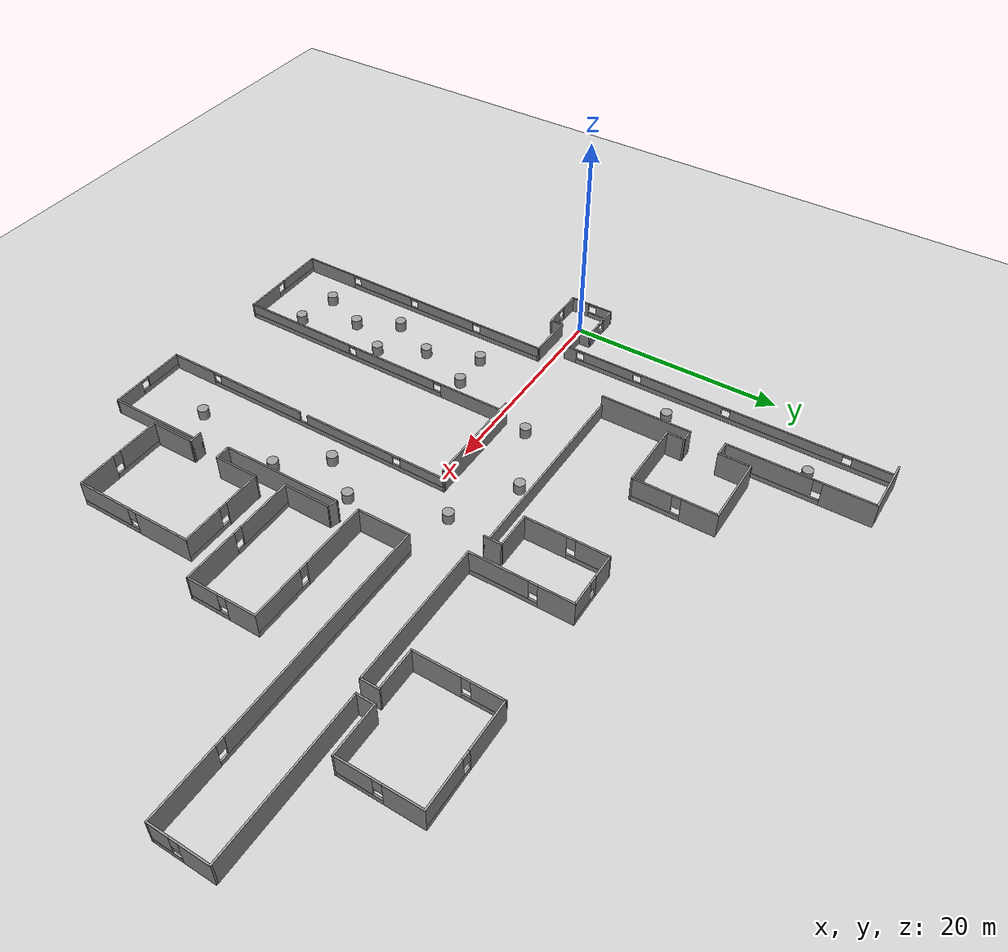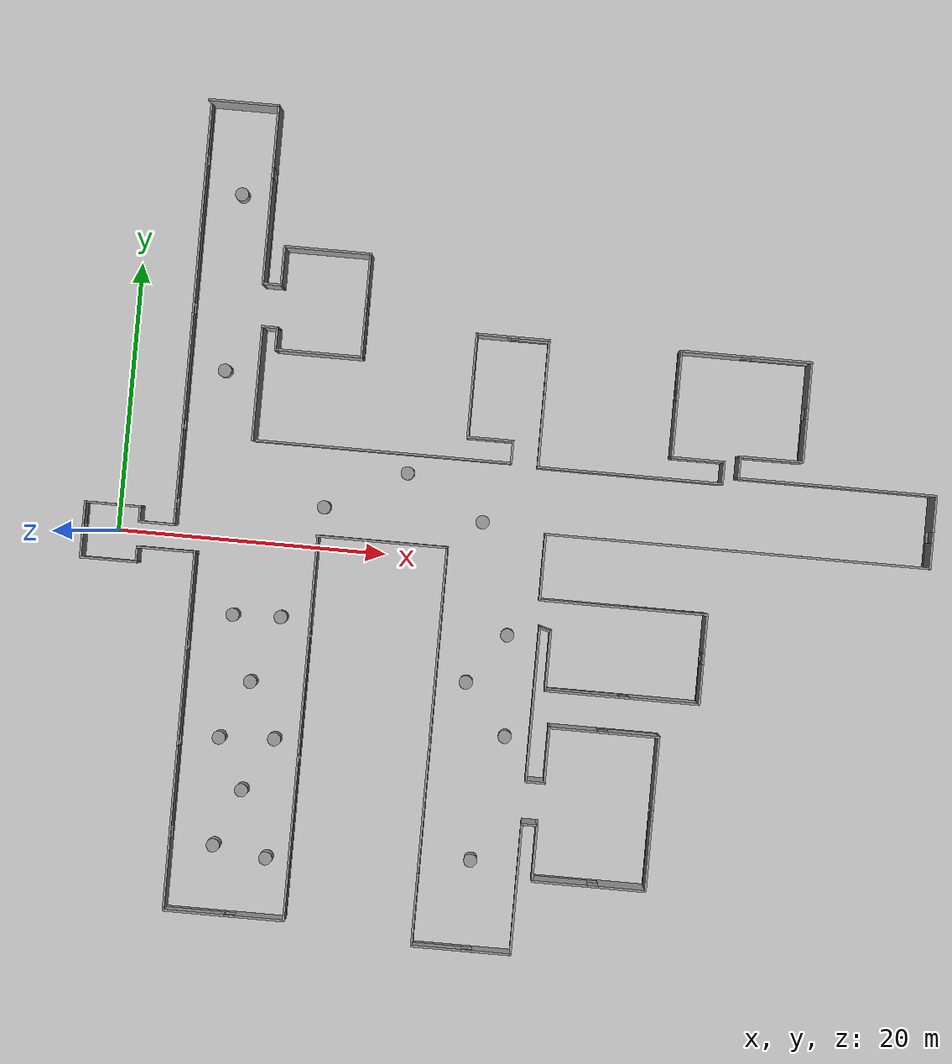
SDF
<sdf version="1.7">
 <world name="default">
  <light name="sun" type="directional">
   <pose>0 0 10 0 -0 0</pose>
   <diffuse>0.8 0.8 0.8 1</diffuse>
   <specular>0.2 0.2 0.2 1</specular>
   <attenuation>
    <range>1000</range>
    <constant>0.9</constant>
    <linear>0.01</linear>
    <quadratic>0.001</quadratic>
   </attenuation>
   <direction>-0.5 0.1 -0.9</direction>
   <spot><inner_angle>0</inner_angle><outer_angle>0</outer_angle><falloff>0</falloff></spot>
  </light>
  <model name="ground_plane">
   <static>1</static>
   <link name="link">
    <collision name="collision">
     <geometry><plane><normal>0 0 1</normal><size>100 100</size></plane></geometry>
     <surface><friction><ode><mu>100</mu><mu2>50</mu2></ode></friction></surface>
    </collision>
    <visual name="visual">
     <cast_shadows>0</cast_shadows>
     <geometry><plane><normal>0 0 1</normal><size>100 100</size></plane></geometry>
     <material>
      <script><uri>file://media/materials/scripts/gazebo.material</uri><name>Gazebo/Grey</name></script>
     </material>
    </visual>
   </link>
  </model>
  <gravity>0 0 -9.8</gravity>
  <magnetic_field>6e-06 2.3e-05 -4.2e-05</magnetic_field>
  <atmosphere type="adiabatic"/>
  <physics type="ode">
   <max_step_size>0.001</max_step_size>
   <real_time_factor>1</real_time_factor>
   <real_time_update_rate>1000</real_time_update_rate>
  </physics>
  <scene><ambient>0.4 0.4 0.4 1</ambient><background>0.7 0.7 0.7 1</background><shadows>1</shadows></scene>
  <spherical_coordinates>
   <surface_model>EARTH_WGS84</surface_model>
   <latitude_deg>0</latitude_deg>
   <longitude_deg>0</longitude_deg>
   <elevation>0</elevation>
   <heading_deg>0</heading_deg>
  </spherical_coordinates>
  <model name="Hummanoid_Test_world">
   <pose>28.8571 1.76082 0 0 -0 0</pose>
   <link name="Wall_1">
    <pose>-29.1696 -3.935 0 0 -0 0</pose>
    <visual name="Wall_1_Visual_0">
     <pose>-1.19344 0 0.75 0 -0 0</pose>
     <geometry><box><size>1.92395 0.15 1.5</size></box></geometry>
     <material>
      <script><uri>file://media/materials/scripts/gazebo.material</uri><name>Gazebo/Grey</name></script>
      <ambient>1 1 1 1</ambient>
     </material>
     <meta><layer>0</layer></meta>
    </visual>
    <collision name="Wall_1_Collision_0">
     <geometry><box><size>1.92395 0.15 1.5</size></box></geometry>
     <pose>-1.19344 0 0.75 0 -0 0</pose>
    </collision>
    <visual name="Wall_1_Visual_1">
     <pose>0.961976 0 0.25 0 -0 0</pose>
     <geometry><box><size>2.38688 0.15 0.5</size></box></geometry>
     <material>
      <script><uri>file://media/materials/scripts/gazebo.material</uri><name>Gazebo/Grey</name></script>
      <ambient>1 1 1 1</ambient>
     </material>
     <meta><layer>0</layer></meta>
    </visual>
    <collision name="Wall_1_Collision_1">
     <geometry><box><size>2.38688 0.15 0.5</size></box></geometry>
     <pose>0.961976 0 0.25 0 -0 0</pose>
    </collision>
    <visual name="Wall_1_Visual_2">
     <pose>1.36198 0 1 0 -0 0</pose>
     <geometry><box><size>1.58688 0.15 1</size></box></geometry>
     <material>
      <script><uri>file://media/materials/scripts/gazebo.material</uri><name>Gazebo/Grey</name></script>
      <ambient>1 1 1 1</ambient>
     </material>
     <meta><layer>0</layer></meta>
    </visual>
    <collision name="Wall_1_Collision_2">
     <geometry><box><size>1.58688 0.15 1</size></box></geometry>
     <pose>1.36198 0 1 0 -0 0</pose>
    </collision>
    <visual name="Wall_1_Visual_3">
     <pose>0.168535 0 1.4 0 -0 0</pose>
     <geometry><box><size>0.8 0.15 0.2</size></box></geometry>
     <material>
      <script><uri>file://media/materials/scripts/gazebo.material</uri><name>Gazebo/Grey</name></script>
      <ambient>1 1 1 1</ambient>
     </material>
     <meta><layer>0</layer></meta>
    </visual>
    <collision name="Wall_1_Collision_3">
     <geometry><box><size>0.8 0.15 0.2</size></box></geometry>
     <pose>0.168535 0 1.4 0 -0 0</pose>
    </collision>
   </link>
   <link name="Wall_10">
    <collision name="Wall_10_Collision">
     <geometry><box><size>2.75 0.15 1.5</size></box></geometry>
     <pose>0 0 0.75 0 -0 0</pose>
    </collision>
    <visual name="Wall_10_Visual">
     <pose>0 0 0.75 0 -0 0</pose>
     <geometry><box><size>2.75 0.15 1.5</size></box></geometry>
     <material>
      <script><uri>file://media/materials/scripts/gazebo.material</uri><name>Gazebo/Grey</name></script>
      <ambient>1 1 1 1</ambient>
     </material>
     <meta><layer>0</layer></meta>
    </visual>
    <pose>-25.85 -0.935 0 0 -0 0</pose>
   </link>
   <link name="Wall_11">
    <pose>-24.55 14.74 0 0 -0 1.5708</pose>
    <visual name="Wall_11_Visual_0">
     <pose>-15.1239 0 0.75 0 -0 0</pose>
     <geometry><box><size>1.25227 0.15 1.5</size></box></geometry>
     <material>
      <script><uri>file://media/materials/scripts/gazebo.material</uri><name>Gazebo/Grey</name></script>
      <ambient>1 1 1 1</ambient>
     </material>
     <meta><layer>0</layer></meta>
    </visual>
    <collision name="Wall_11_Collision_0">
     <geometry><box><size>1.25227 0.15 1.5</size></box></geometry>
     <pose>-15.1239 0 0.75 0 -0 0</pose>
    </collision>
    <visual name="Wall_11_Visual_1">
     <pose>0.626135 0 0.25 0 -0 0</pose>
     <geometry><box><size>30.2477 0.15 0.5</size></box></geometry>
     <material>
      <script><uri>file://media/materials/scripts/gazebo.material</uri><name>Gazebo/Grey</name></script>
      <ambient>1 1 1 1</ambient>
     </material>
     <meta><layer>0</layer></meta>
    </visual>
    <collision name="Wall_11_Collision_1">
     <geometry><box><size>30.2477 0.15 0.5</size></box></geometry>
     <pose>0.626135 0 0.25 0 -0 0</pose>
    </collision>
    <visual name="Wall_11_Visual_2">
     <pose>-11.1577 0 1 0 -0 0</pose>
     <geometry><box><size>5.08 0.15 1</size></box></geometry>
     <material>
      <script><uri>file://media/materials/scripts/gazebo.material</uri><name>Gazebo/Grey</name></script>
      <ambient>1 1 1 1</ambient>
     </material>
     <meta><layer>0</layer></meta>
    </visual>
    <collision name="Wall_11_Collision_2">
     <geometry><box><size>5.08 0.15 1</size></box></geometry>
     <pose>-11.1577 0 1 0 -0 0</pose>
    </collision>
    <visual name="Wall_11_Visual_3">
     <pose>-3.87047 0 1 0 -0 0</pose>
     <geometry><box><size>7.89451 0.15 1</size></box></geometry>
     <material>
      <script><uri>file://media/materials/scripts/gazebo.material</uri><name>Gazebo/Grey</name></script>
      <ambient>1 1 1 1</ambient>
     </material>
     <meta><layer>0</layer></meta>
    </visual>
    <collision name="Wall_11_Collision_3">
     <geometry><box><size>7.89451 0.15 1</size></box></geometry>
     <pose>-3.87047 0 1 0 -0 0</pose>
    </collision>
    <visual name="Wall_11_Visual_4">
     <pose>6.00999 0 1 0 -0 0</pose>
     <geometry><box><size>10.2664 0.15 1</size></box></geometry>
     <material>
      <script><uri>file://media/materials/scripts/gazebo.material</uri><name>Gazebo/Grey</name></script>
      <ambient>1 1 1 1</ambient>
     </material>
     <meta><layer>0</layer></meta>
    </visual>
    <collision name="Wall_11_Collision_4">
     <geometry><box><size>10.2664 0.15 1</size></box></geometry>
     <pose>6.00999 0 1 0 -0 0</pose>
    </collision>
    <visual name="Wall_11_Visual_5">
     <pose>13.8466 0 1 0 -0 0</pose>
     <geometry><box><size>3.80681 0.15 1</size></box></geometry>
     <material>
      <script><uri>file://media/materials/scripts/gazebo.material</uri><name>Gazebo/Grey</name></script>
      <ambient>1 1 1 1</ambient>
     </material>
     <meta><layer>0</layer></meta>
    </visual>
    <collision name="Wall_11_Collision_5">
     <geometry><box><size>3.80681 0.15 1</size></box></geometry>
     <pose>13.8466 0 1 0 -0 0</pose>
    </collision>
    <visual name="Wall_11_Visual_6">
     <pose>-14.0977 0 1.4 0 -0 0</pose>
     <geometry><box><size>0.8 0.15 0.2</size></box></geometry>
     <material>
      <script><uri>file://media/materials/scripts/gazebo.material</uri><name>Gazebo/Grey</name></script>
      <ambient>1 1 1 1</ambient>
     </material>
     <meta><layer>0</layer></meta>
    </visual>
    <collision name="Wall_11_Collision_6">
     <geometry><box><size>0.8 0.15 0.2</size></box></geometry>
     <pose>-14.0977 0 1.4 0 -0 0</pose>
    </collision>
    <visual name="Wall_11_Visual_7">
     <pose>-8.21773 0 1.4 0 -0 0</pose>
     <geometry><box><size>0.8 0.15 0.2</size></box></geometry>
     <material>
      <script><uri>file://media/materials/scripts/gazebo.material</uri><name>Gazebo/Grey</name></script>
      <ambient>1 1 1 1</ambient>
     </material>
     <meta><layer>0</layer></meta>
    </visual>
    <collision name="Wall_11_Collision_7">
     <geometry><box><size>0.8 0.15 0.2</size></box></geometry>
     <pose>-8.21773 0 1.4 0 -0 0</pose>
    </collision>
    <visual name="Wall_11_Visual_8">
     <pose>0.476782 0 1.4 0 -0 0</pose>
     <geometry><box><size>0.8 0.15 0.2</size></box></geometry>
     <material>
      <script><uri>file://media/materials/scripts/gazebo.material</uri><name>Gazebo/Grey</name></script>
      <ambient>1 1 1 1</ambient>
     </material>
     <meta><layer>0</layer></meta>
    </visual>
    <collision name="Wall_11_Collision_8">
     <geometry><box><size>0.8 0.15 0.2</size></box></geometry>
     <pose>0.476782 0 1.4 0 -0 0</pose>
    </collision>
    <visual name="Wall_11_Visual_9">
     <pose>11.5432 0 1.4 0 -0 0</pose>
     <geometry><box><size>0.8 0.15 0.2</size></box></geometry>
     <material>
      <script><uri>file://media/materials/scripts/gazebo.material</uri><name>Gazebo/Grey</name></script>
      <ambient>1 1 1 1</ambient>
     </material>
     <meta><layer>0</layer></meta>
    </visual>
    <collision name="Wall_11_Collision_9">
     <geometry><box><size>0.8 0.15 0.2</size></box></geometry>
     <pose>11.5432 0 1.4 0 -0 0</pose>
    </collision>
   </link>
   <link name="Wall_12">
    <collision name="Wall_12_Collision">
     <geometry><box><size>5.25 0.15 2.5</size></box></geometry>
     <pose>0 0 1.25 0 -0 0</pose>
    </collision>
    <visual name="Wall_12_Visual">
     <pose>0 0 1.25 0 -0 0</pose>
     <geometry><box><size>5.25 0.15 2.5</size></box></geometry>
     <material>
      <script><uri>file://media/materials/scripts/gazebo.material</uri><name>Gazebo/Grey</name></script>
      <ambient>1 1 1 1</ambient>
     </material>
     <meta><layer>0</layer></meta>
    </visual>
    <pose>-22 30.415 0 0 -0 0</pose>
   </link>
   <link name="Wall_13">
    <pose>-19.45 23.865 0 0 -0 -1.5708</pose>
    <visual name="Wall_13_Visual_0">
     <pose>-4.31474 0 1.25 0 -0 0</pose>
     <geometry><box><size>4.62052 0.15 2.5</size></box></geometry>
     <material>
      <script><uri>file://media/materials/scripts/gazebo.material</uri><name>Gazebo/Grey</name></script>
      <ambient>1 1 1 1</ambient>
     </material>
     <meta><layer>0</layer></meta>
    </visual>
    <collision name="Wall_13_Collision_0">
     <geometry><box><size>4.62052 0.15 2.5</size></box></geometry>
     <pose>-4.31474 0 1.25 0 -0 0</pose>
    </collision>
    <visual name="Wall_13_Visual_1">
     <pose>2.31026 0 0.25 0 -0 0</pose>
     <geometry><box><size>8.62948 0.15 0.5</size></box></geometry>
     <material>
      <script><uri>file://media/materials/scripts/gazebo.material</uri><name>Gazebo/Grey</name></script>
      <ambient>1 1 1 1</ambient>
     </material>
     <meta><layer>0</layer></meta>
    </visual>
    <collision name="Wall_13_Collision_1">
     <geometry><box><size>8.62948 0.15 0.5</size></box></geometry>
     <pose>2.31026 0 0.25 0 -0 0</pose>
    </collision>
    <visual name="Wall_13_Visual_2">
     <pose>2.71026 0 1.5 0 -0 0</pose>
     <geometry><box><size>7.82948 0.15 2</size></box></geometry>
     <material>
      <script><uri>file://media/materials/scripts/gazebo.material</uri><name>Gazebo/Grey</name></script>
      <ambient>1 1 1 1</ambient>
     </material>
     <meta><layer>0</layer></meta>
    </visual>
    <collision name="Wall_13_Collision_2">
     <geometry><box><size>7.82948 0.15 2</size></box></geometry>
     <pose>2.71026 0 1.5 0 -0 0</pose>
    </collision>
    <visual name="Wall_13_Visual_3">
     <pose>-1.60448 0 1.9 0 -0 0</pose>
     <geometry><box><size>0.8 0.15 1.2</size></box></geometry>
     <material>
      <script><uri>file://media/materials/scripts/gazebo.material</uri><name>Gazebo/Grey</name></script>
      <ambient>1 1 1 1</ambient>
     </material>
     <meta><layer>0</layer></meta>
    </visual>
    <collision name="Wall_13_Collision_3">
     <geometry><box><size>0.8 0.15 1.2</size></box></geometry>
     <pose>-1.60448 0 1.9 0 -0 0</pose>
    </collision>
   </link>
   <link name="Wall_17">
    <collision name="Wall_17_Collision">
     <geometry><box><size>1.5 0.15 2.5</size></box></geometry>
     <pose>0 0 1.25 0 -0 0</pose>
    </collision>
    <visual name="Wall_17_Visual">
     <pose>0 0 1.25 0 -0 0</pose>
     <geometry><box><size>1.5 0.15 2.5</size></box></geometry>
     <material>
      <script><uri>file://media/materials/scripts/gazebo.material</uri><name>Gazebo/Grey</name></script>
      <ambient>1 1 1 1</ambient>
     </material>
     <meta><layer>0</layer></meta>
    </visual>
    <pose>-18.775 17.315 0 0 -0 0</pose>
   </link>
   <link name="Wall_18">
    <collision name="Wall_18_Collision">
     <geometry><box><size>3 0.15 2.5</size></box></geometry>
     <pose>0 0 1.25 0 -0 0</pose>
    </collision>
    <visual name="Wall_18_Visual">
     <pose>0 0 1.25 0 -0 0</pose>
     <geometry><box><size>3 0.15 2.5</size></box></geometry>
     <material>
      <script><uri>file://media/materials/scripts/gazebo.material</uri><name>Gazebo/Grey</name></script>
      <ambient>1 1 1 1</ambient>
     </material>
     <meta><layer>0</layer></meta>
    </visual>
    <pose>-18.1 18.74 0 0 -0 1.5708</pose>
   </link>
   <link name="Wall_19">
    <collision name="Wall_19_Collision">
     <geometry><box><size>6.5 0.15 2.5</size></box></geometry>
     <pose>0 0 1.25 0 -0 0</pose>
    </collision>
    <visual name="Wall_19_Visual">
     <pose>0 0 1.25 0 -0 0</pose>
     <geometry><box><size>6.5 0.15 2.5</size></box></geometry>
     <material>
      <script><uri>file://media/materials/scripts/gazebo.material</uri><name>Gazebo/Grey</name></script>
      <ambient>1 1 1 1</ambient>
     </material>
     <meta><layer>0</layer></meta>
    </visual>
    <pose>-14.925 20.165 0 0 -0 0</pose>
   </link>
   <link name="Wall_20">
    <pose>-11.75 16.365 0 0 -0 -1.5708</pose>
    <visual name="Wall_20_Visual_0">
     <pose>-2.24729 0 1.25 0 -0 0</pose>
     <geometry><box><size>3.25542 0.15 2.5</size></box></geometry>
     <material>
      <script><uri>file://media/materials/scripts/gazebo.material</uri><name>Gazebo/Grey</name></script>
      <ambient>1 1 1 1</ambient>
     </material>
     <meta><layer>0</layer></meta>
    </visual>
    <collision name="Wall_20_Collision_0">
     <geometry><box><size>3.25542 0.15 2.5</size></box></geometry>
     <pose>-2.24729 0 1.25 0 -0 0</pose>
    </collision>
    <visual name="Wall_20_Visual_1">
     <pose>1.62771 0 0.25 0 -0 0</pose>
     <geometry><box><size>4.49458 0.15 0.5</size></box></geometry>
     <material>
      <script><uri>file://media/materials/scripts/gazebo.material</uri><name>Gazebo/Grey</name></script>
      <ambient>1 1 1 1</ambient>
     </material>
     <meta><layer>0</layer></meta>
    </visual>
    <collision name="Wall_20_Collision_1">
     <geometry><box><size>4.49458 0.15 0.5</size></box></geometry>
     <pose>1.62771 0 0.25 0 -0 0</pose>
    </collision>
    <visual name="Wall_20_Visual_2">
     <pose>2.02771 0 1.5 0 -0 0</pose>
     <geometry><box><size>3.69458 0.15 2</size></box></geometry>
     <material>
      <script><uri>file://media/materials/scripts/gazebo.material</uri><name>Gazebo/Grey</name></script>
      <ambient>1 1 1 1</ambient>
     </material>
     <meta><layer>0</layer></meta>
    </visual>
    <collision name="Wall_20_Collision_2">
     <geometry><box><size>3.69458 0.15 2</size></box></geometry>
     <pose>2.02771 0 1.5 0 -0 0</pose>
    </collision>
    <visual name="Wall_20_Visual_3">
     <pose>-0.219584 0 1.9 0 -0 0</pose>
     <geometry><box><size>0.8 0.15 1.2</size></box></geometry>
     <material>
      <script><uri>file://media/materials/scripts/gazebo.material</uri><name>Gazebo/Grey</name></script>
      <ambient>1 1 1 1</ambient>
     </material>
     <meta><layer>0</layer></meta>
    </visual>
    <collision name="Wall_20_Collision_3">
     <geometry><box><size>0.8 0.15 1.2</size></box></geometry>
     <pose>-0.219584 0 1.9 0 -0 0</pose>
    </collision>
   </link>
   <link name="Wall_21">
    <collision name="Wall_21_Collision">
     <geometry><box><size>6.5 0.15 2.5</size></box></geometry>
     <pose>0 0 1.25 0 -0 0</pose>
    </collision>
    <visual name="Wall_21_Visual">
     <pose>0 0 1.25 0 -0 0</pose>
     <geometry><box><size>6.5 0.15 2.5</size></box></geometry>
     <material>
      <script><uri>file://media/materials/scripts/gazebo.material</uri><name>Gazebo/Grey</name></script>
      <ambient>1 1 1 1</ambient>
     </material>
     <meta><layer>0</layer></meta>
    </visual>
    <pose>-14.925 12.565 0 0 -0 3.14159</pose>
   </link>
   <link name="Wall_22">
    <collision name="Wall_22_Collision">
     <geometry><box><size>1.75 0.15 2.5</size></box></geometry>
     <pose>0 0 1.25 0 -0 0</pose>
    </collision>
    <visual name="Wall_22_Visual">
     <pose>0 0 1.25 0 -0 0</pose>
     <geometry><box><size>1.75 0.15 2.5</size></box></geometry>
     <material>
      <script><uri>file://media/materials/scripts/gazebo.material</uri><name>Gazebo/Grey</name></script>
      <ambient>1 1 1 1</ambient>
     </material>
     <meta><layer>0</layer></meta>
    </visual>
    <pose>-18.1 13.365 0 0 -0 1.5708</pose>
   </link>
   <link name="Wall_23">
    <collision name="Wall_23_Collision">
     <geometry><box><size>1.25 0.15 2.5</size></box></geometry>
     <pose>0 0 1.25 0 -0 0</pose>
    </collision>
    <visual name="Wall_23_Visual">
     <pose>0 0 1.25 0 -0 0</pose>
     <geometry><box><size>1.25 0.15 2.5</size></box></geometry>
     <material>
      <script><uri>file://media/materials/scripts/gazebo.material</uri><name>Gazebo/Grey</name></script>
      <ambient>1 1 1 1</ambient>
     </material>
     <meta><layer>0</layer></meta>
    </visual>
    <pose>-18.65 14.165 0 0 -0 3.14159</pose>
   </link>
   <link name="Wall_24">
    <collision name="Wall_24_Collision">
     <geometry><box><size>8.5 0.15 2.5</size></box></geometry>
     <pose>0 0 1.25 0 -0 0</pose>
    </collision>
    <visual name="Wall_24_Visual">
     <pose>0 0 1.25 0 -0 0</pose>
     <geometry><box><size>8.5 0.15 2.5</size></box></geometry>
     <material>
      <script><uri>file://media/materials/scripts/gazebo.material</uri><name>Gazebo/Grey</name></script>
      <ambient>1 1 1 1</ambient>
     </material>
     <meta><layer>0</layer></meta>
    </visual>
    <pose>-19.2 9.99 0 0 -0 -1.5708</pose>
   </link>
   <link name="Wall_25">
    <collision name="Wall_25_Collision">
     <geometry><box><size>19.25 0.15 1.5</size></box></geometry>
     <pose>0 0 0.75 0 -0 0</pose>
    </collision>
    <visual name="Wall_25_Visual">
     <pose>0 0 0.75 0 -0 0</pose>
     <geometry><box><size>19.25 0.15 1.5</size></box></geometry>
     <material>
      <script><uri>file://media/materials/scripts/gazebo.material</uri><name>Gazebo/Grey</name></script>
      <ambient>1 1 1 1</ambient>
     </material>
     <meta><layer>0</layer></meta>
    </visual>
    <pose>-9.65 5.815 0 0 -0 0</pose>
   </link>
   <link name="Wall_26">
    <collision name="Wall_26_Collision">
     <geometry><box><size>1.75 0.15 2.5</size></box></geometry>
     <pose>0 0 1.25 0 -0 0</pose>
    </collision>
    <visual name="Wall_26_Visual">
     <pose>0 0 1.25 0 -0 0</pose>
     <geometry><box><size>1.75 0.15 2.5</size></box></geometry>
     <material>
      <script><uri>file://media/materials/scripts/gazebo.material</uri><name>Gazebo/Grey</name></script>
      <ambient>1 1 1 1</ambient>
     </material>
     <meta><layer>0</layer></meta>
    </visual>
    <pose>-0.100001 6.615 0 0 -0 1.5708</pose>
   </link>
   <link name="Wall_27">
    <collision name="Wall_27_Collision">
     <geometry><box><size>3.5 0.15 2.5</size></box></geometry>
     <pose>0 0 1.25 0 -0 0</pose>
    </collision>
    <visual name="Wall_27_Visual">
     <pose>0 0 1.25 0 -0 0</pose>
     <geometry><box><size>3.5 0.15 2.5</size></box></geometry>
     <material>
      <script><uri>file://media/materials/scripts/gazebo.material</uri><name>Gazebo/Grey</name></script>
      <ambient>1 1 1 1</ambient>
     </material>
     <meta><layer>0</layer></meta>
    </visual>
    <pose>-1.775 7.415 0 0 -0 3.14159</pose>
   </link>
   <link name="Wall_28">
    <pose>-3.45 11.215 0 0 -0 1.5708</pose>
    <visual name="Wall_28_Visual_0">
     <pose>-1.91382 0 1.25 0 -0 0</pose>
     <geometry><box><size>3.92235 0.15 2.5</size></box></geometry>
     <material>
      <script><uri>file://media/materials/scripts/gazebo.material</uri><name>Gazebo/Grey</name></script>
      <ambient>1 1 1 1</ambient>
     </material>
     <meta><layer>0</layer></meta>
    </visual>
    <collision name="Wall_28_Collision_0">
     <geometry><box><size>3.92235 0.15 2.5</size></box></geometry>
     <pose>-1.91382 0 1.25 0 -0 0</pose>
    </collision>
    <visual name="Wall_28_Visual_1">
     <pose>1.96118 0 0.25 0 -0 0</pose>
     <geometry><box><size>3.82765 0.15 0.5</size></box></geometry>
     <material>
      <script><uri>file://media/materials/scripts/gazebo.material</uri><name>Gazebo/Grey</name></script>
      <ambient>1 1 1 1</ambient>
     </material>
     <meta><layer>0</layer></meta>
    </visual>
    <collision name="Wall_28_Collision_1">
     <geometry><box><size>3.82765 0.15 0.5</size></box></geometry>
     <pose>1.96118 0 0.25 0 -0 0</pose>
    </collision>
    <visual name="Wall_28_Visual_2">
     <pose>2.36118 0 1.5 0 -0 0</pose>
     <geometry><box><size>3.02765 0.15 2</size></box></geometry>
     <material>
      <script><uri>file://media/materials/scripts/gazebo.material</uri><name>Gazebo/Grey</name></script>
      <ambient>1 1 1 1</ambient>
     </material>
     <meta><layer>0</layer></meta>
    </visual>
    <collision name="Wall_28_Collision_2">
     <geometry><box><size>3.02765 0.15 2</size></box></geometry>
     <pose>2.36118 0 1.5 0 -0 0</pose>
    </collision>
    <visual name="Wall_28_Visual_3">
     <pose>0.447352 0 1.9 0 -0 0</pose>
     <geometry><box><size>0.8 0.15 1.2</size></box></geometry>
     <material>
      <script><uri>file://media/materials/scripts/gazebo.material</uri><name>Gazebo/Grey</name></script>
      <ambient>1 1 1 1</ambient>
     </material>
     <meta><layer>0</layer></meta>
    </visual>
    <collision name="Wall_28_Collision_3">
     <geometry><box><size>0.8 0.15 1.2</size></box></geometry>
     <pose>0.447352 0 1.9 0 -0 0</pose>
    </collision>
   </link>
   <link name="Wall_29">
    <pose>-0.775 15.015 0 0 -0 0</pose>
    <visual name="Wall_29_Visual_0">
     <pose>-1.5701 0 1.25 0 -0 0</pose>
     <geometry><box><size>2.35979 0.15 2.5</size></box></geometry>
     <material>
      <script><uri>file://media/materials/scripts/gazebo.material</uri><name>Gazebo/Grey</name></script>
      <ambient>1 1 1 1</ambient>
     </material>
     <meta><layer>0</layer></meta>
    </visual>
    <collision name="Wall_29_Collision_0">
     <geometry><box><size>2.35979 0.15 2.5</size></box></geometry>
     <pose>-1.5701 0 1.25 0 -0 0</pose>
    </collision>
    <visual name="Wall_29_Visual_1">
     <pose>1.1799 0 0.25 0 -0 0</pose>
     <geometry><box><size>3.14021 0.15 0.5</size></box></geometry>
     <material>
      <script><uri>file://media/materials/scripts/gazebo.material</uri><name>Gazebo/Grey</name></script>
      <ambient>1 1 1 1</ambient>
     </material>
     <meta><layer>0</layer></meta>
    </visual>
    <collision name="Wall_29_Collision_1">
     <geometry><box><size>3.14021 0.15 0.5</size></box></geometry>
     <pose>1.1799 0 0.25 0 -0 0</pose>
    </collision>
    <visual name="Wall_29_Visual_2">
     <pose>1.5799 0 1.5 0 -0 0</pose>
     <geometry><box><size>2.34021 0.15 2</size></box></geometry>
     <material>
      <script><uri>file://media/materials/scripts/gazebo.material</uri><name>Gazebo/Grey</name></script>
      <ambient>1 1 1 1</ambient>
     </material>
     <meta><layer>0</layer></meta>
    </visual>
    <collision name="Wall_29_Collision_2">
     <geometry><box><size>2.34021 0.15 2</size></box></geometry>
     <pose>1.5799 0 1.5 0 -0 0</pose>
    </collision>
    <visual name="Wall_29_Visual_3">
     <pose>0.009794 0 1.9 0 -0 0</pose>
     <geometry><box><size>0.8 0.15 1.2</size></box></geometry>
     <material>
      <script><uri>file://media/materials/scripts/gazebo.material</uri><name>Gazebo/Grey</name></script>
      <ambient>1 1 1 1</ambient>
     </material>
     <meta><layer>0</layer></meta>
    </visual>
    <collision name="Wall_29_Collision_3">
     <geometry><box><size>0.8 0.15 1.2</size></box></geometry>
     <pose>0.009794 0 1.9 0 -0 0</pose>
    </collision>
   </link>
   <link name="Wall_30">
    <pose>1.9 10.34 0 0 -0 -1.5708</pose>
    <visual name="Wall_30_Visual_0">
     <pose>-3.12917 0 1.25 0 -0 0</pose>
     <geometry><box><size>3.24166 0.15 2.5</size></box></geometry>
     <material>
      <script><uri>file://media/materials/scripts/gazebo.material</uri><name>Gazebo/Grey</name></script>
      <ambient>1 1 1 1</ambient>
     </material>
     <meta><layer>0</layer></meta>
    </visual>
    <collision name="Wall_30_Collision_0">
     <geometry><box><size>3.24166 0.15 2.5</size></box></geometry>
     <pose>-3.12917 0 1.25 0 -0 0</pose>
    </collision>
    <visual name="Wall_30_Visual_1">
     <pose>1.62083 0 0.25 0 -0 0</pose>
     <geometry><box><size>6.25834 0.15 0.5</size></box></geometry>
     <material>
      <script><uri>file://media/materials/scripts/gazebo.material</uri><name>Gazebo/Grey</name></script>
      <ambient>1 1 1 1</ambient>
     </material>
     <meta><layer>0</layer></meta>
    </visual>
    <collision name="Wall_30_Collision_1">
     <geometry><box><size>6.25834 0.15 0.5</size></box></geometry>
     <pose>1.62083 0 0.25 0 -0 0</pose>
    </collision>
    <visual name="Wall_30_Visual_2">
     <pose>2.02083 0 1.5 0 -0 0</pose>
     <geometry><box><size>5.45834 0.15 2</size></box></geometry>
     <material>
      <script><uri>file://media/materials/scripts/gazebo.material</uri><name>Gazebo/Grey</name></script>
      <ambient>1 1 1 1</ambient>
     </material>
     <meta><layer>0</layer></meta>
    </visual>
    <collision name="Wall_30_Collision_2">
     <geometry><box><size>5.45834 0.15 2</size></box></geometry>
     <pose>2.02083 0 1.5 0 -0 0</pose>
    </collision>
    <visual name="Wall_30_Visual_3">
     <pose>-1.10834 0 1.9 0 -0 0</pose>
     <geometry><box><size>0.8 0.15 1.2</size></box></geometry>
     <material>
      <script><uri>file://media/materials/scripts/gazebo.material</uri><name>Gazebo/Grey</name></script>
      <ambient>1 1 1 1</ambient>
     </material>
     <meta><layer>0</layer></meta>
    </visual>
    <collision name="Wall_30_Collision_3">
     <geometry><box><size>0.8 0.15 1.2</size></box></geometry>
     <pose>-1.10834 0 1.9 0 -0 0</pose>
    </collision>
   </link>
   <link name="Wall_31">
    <collision name="Wall_31_Collision">
     <geometry><box><size>13.75 0.15 2.5</size></box></geometry>
     <pose>0 0 1.25 0 -0 0</pose>
    </collision>
    <visual name="Wall_31_Visual">
     <pose>0 0 1.25 0 -0 0</pose>
     <geometry><box><size>13.75 0.15 2.5</size></box></geometry>
     <material>
      <script><uri>file://media/materials/scripts/gazebo.material</uri><name>Gazebo/Grey</name></script>
      <ambient>1 1 1 1</ambient>
     </material>
     <meta><layer>0</layer></meta>
    </visual>
    <pose>8.7 5.665 0 0 -0 0</pose>
   </link>
   <link name="Wall_32">
    <collision name="Wall_32_Collision">
     <geometry><box><size>1.75 0.15 2.5</size></box></geometry>
     <pose>0 0 1.25 0 -0 0</pose>
    </collision>
    <visual name="Wall_32_Visual">
     <pose>0 0 1.25 0 -0 0</pose>
     <geometry><box><size>1.75 0.15 2.5</size></box></geometry>
     <material>
      <script><uri>file://media/materials/scripts/gazebo.material</uri><name>Gazebo/Grey</name></script>
      <ambient>1 1 1 1</ambient>
     </material>
     <meta><layer>0</layer></meta>
    </visual>
    <pose>15.5 6.465 0 0 -0 1.5708</pose>
   </link>
   <link name="Wall_33">
    <collision name="Wall_33_Collision">
     <geometry><box><size>4 0.15 2.5</size></box></geometry>
     <pose>0 0 1.25 0 -0 0</pose>
    </collision>
    <visual name="Wall_33_Visual">
     <pose>0 0 1.25 0 -0 0</pose>
     <geometry><box><size>4 0.15 2.5</size></box></geometry>
     <material>
      <script><uri>file://media/materials/scripts/gazebo.material</uri><name>Gazebo/Grey</name></script>
      <ambient>1 1 1 1</ambient>
     </material>
     <meta><layer>0</layer></meta>
    </visual>
    <pose>13.575 7.265 0 0 -0 3.14159</pose>
   </link>
   <link name="Wall_34">
    <pose>11.65 11.19 0 0 -0 1.5708</pose>
    <visual name="Wall_34_Visual_0">
     <pose>-1.85682 0 1.25 0 -0 0</pose>
     <geometry><box><size>4.28636 0.15 2.5</size></box></geometry>
     <material>
      <script><uri>file://media/materials/scripts/gazebo.material</uri><name>Gazebo/Grey</name></script>
      <ambient>1 1 1 1</ambient>
     </material>
     <meta><layer>0</layer></meta>
    </visual>
    <collision name="Wall_34_Collision_0">
     <geometry><box><size>4.28636 0.15 2.5</size></box></geometry>
     <pose>-1.85682 0 1.25 0 -0 0</pose>
    </collision>
    <visual name="Wall_34_Visual_1">
     <pose>2.14318 0 0.25 0 -0 0</pose>
     <geometry><box><size>3.71364 0.15 0.5</size></box></geometry>
     <material>
      <script><uri>file://media/materials/scripts/gazebo.material</uri><name>Gazebo/Grey</name></script>
      <ambient>1 1 1 1</ambient>
     </material>
     <meta><layer>0</layer></meta>
    </visual>
    <collision name="Wall_34_Collision_1">
     <geometry><box><size>3.71364 0.15 0.5</size></box></geometry>
     <pose>2.14318 0 0.25 0 -0 0</pose>
    </collision>
    <visual name="Wall_34_Visual_2">
     <pose>2.54318 0 1.5 0 -0 0</pose>
     <geometry><box><size>2.91364 0.15 2</size></box></geometry>
     <material>
      <script><uri>file://media/materials/scripts/gazebo.material</uri><name>Gazebo/Grey</name></script>
      <ambient>1 1 1 1</ambient>
     </material>
     <meta><layer>0</layer></meta>
    </visual>
    <collision name="Wall_34_Collision_2">
     <geometry><box><size>2.91364 0.15 2</size></box></geometry>
     <pose>2.54318 0 1.5 0 -0 0</pose>
    </collision>
    <visual name="Wall_34_Visual_3">
     <pose>0.686362 0 1.9 0 -0 0</pose>
     <geometry><box><size>0.8 0.15 1.2</size></box></geometry>
     <material>
      <script><uri>file://media/materials/scripts/gazebo.material</uri><name>Gazebo/Grey</name></script>
      <ambient>1 1 1 1</ambient>
     </material>
     <meta><layer>0</layer></meta>
    </visual>
    <collision name="Wall_34_Collision_3">
     <geometry><box><size>0.8 0.15 1.2</size></box></geometry>
     <pose>0.686362 0 1.9 0 -0 0</pose>
    </collision>
   </link>
   <link name="Wall_35">
    <pose>16.45 15.115 0 0 -0 0</pose>
    <visual name="Wall_35_Visual_0">
     <pose>-2.5777 0 1.25 0 -0 0</pose>
     <geometry><box><size>4.59461 0.15 2.5</size></box></geometry>
     <material>
      <script><uri>file://media/materials/scripts/gazebo.material</uri><name>Gazebo/Grey</name></script>
      <ambient>1 1 1 1</ambient>
     </material>
     <meta><layer>0</layer></meta>
    </visual>
    <collision name="Wall_35_Collision_0">
     <geometry><box><size>4.59461 0.15 2.5</size></box></geometry>
     <pose>-2.5777 0 1.25 0 -0 0</pose>
    </collision>
    <visual name="Wall_35_Visual_1">
     <pose>2.2973 0 0.25 0 -0 0</pose>
     <geometry><box><size>5.15539 0.15 0.5</size></box></geometry>
     <material>
      <script><uri>file://media/materials/scripts/gazebo.material</uri><name>Gazebo/Grey</name></script>
      <ambient>1 1 1 1</ambient>
     </material>
     <meta><layer>0</layer></meta>
    </visual>
    <collision name="Wall_35_Collision_1">
     <geometry><box><size>5.15539 0.15 0.5</size></box></geometry>
     <pose>2.2973 0 0.25 0 -0 0</pose>
    </collision>
    <visual name="Wall_35_Visual_2">
     <pose>2.6973 0 1.5 0 -0 0</pose>
     <geometry><box><size>4.35539 0.15 2</size></box></geometry>
     <material>
      <script><uri>file://media/materials/scripts/gazebo.material</uri><name>Gazebo/Grey</name></script>
      <ambient>1 1 1 1</ambient>
     </material>
     <meta><layer>0</layer></meta>
    </visual>
    <collision name="Wall_35_Collision_2">
     <geometry><box><size>4.35539 0.15 2</size></box></geometry>
     <pose>2.6973 0 1.5 0 -0 0</pose>
    </collision>
    <visual name="Wall_35_Visual_3">
     <pose>0.119606 0 1.9 0 -0 0</pose>
     <geometry><box><size>0.8 0.15 1.2</size></box></geometry>
     <material>
      <script><uri>file://media/materials/scripts/gazebo.material</uri><name>Gazebo/Grey</name></script>
      <ambient>1 1 1 1</ambient>
     </material>
     <meta><layer>0</layer></meta>
    </visual>
    <collision name="Wall_35_Collision_3">
     <geometry><box><size>0.8 0.15 1.2</size></box></geometry>
     <pose>0.119606 0 1.9 0 -0 0</pose>
    </collision>
   </link>
   <link name="Wall_36">
    <pose>21.25 11.44 0 0 -0 -1.5708</pose>
    <visual name="Wall_36_Visual_0">
     <pose>-2.02567 0 1.25 0 -0 0</pose>
     <geometry><box><size>3.44866 0.15 2.5</size></box></geometry>
     <material>
      <script><uri>file://media/materials/scripts/gazebo.material</uri><name>Gazebo/Grey</name></script>
      <ambient>1 1 1 1</ambient>
     </material>
     <meta><layer>0</layer></meta>
    </visual>
    <collision name="Wall_36_Collision_0">
     <geometry><box><size>3.44866 0.15 2.5</size></box></geometry>
     <pose>-2.02567 0 1.25 0 -0 0</pose>
    </collision>
    <visual name="Wall_36_Visual_1">
     <pose>1.72433 0 0.25 0 -0 0</pose>
     <geometry><box><size>4.05134 0.15 0.5</size></box></geometry>
     <material>
      <script><uri>file://media/materials/scripts/gazebo.material</uri><name>Gazebo/Grey</name></script>
      <ambient>1 1 1 1</ambient>
     </material>
     <meta><layer>0</layer></meta>
    </visual>
    <collision name="Wall_36_Collision_1">
     <geometry><box><size>4.05134 0.15 0.5</size></box></geometry>
     <pose>1.72433 0 0.25 0 -0 0</pose>
    </collision>
    <visual name="Wall_36_Visual_2">
     <pose>2.12433 0 1.5 0 -0 0</pose>
     <geometry><box><size>3.25134 0.15 2</size></box></geometry>
     <material>
      <script><uri>file://media/materials/scripts/gazebo.material</uri><name>Gazebo/Grey</name></script>
      <ambient>1 1 1 1</ambient>
     </material>
     <meta><layer>0</layer></meta>
    </visual>
    <collision name="Wall_36_Collision_2">
     <geometry><box><size>3.25134 0.15 2</size></box></geometry>
     <pose>2.12433 0 1.5 0 -0 0</pose>
    </collision>
    <visual name="Wall_36_Visual_3">
     <pose>0.098663 0 1.9 0 -0 0</pose>
     <geometry><box><size>0.8 0.15 1.2</size></box></geometry>
     <material>
      <script><uri>file://media/materials/scripts/gazebo.material</uri><name>Gazebo/Grey</name></script>
      <ambient>1 1 1 1</ambient>
     </material>
     <meta><layer>0</layer></meta>
    </visual>
    <collision name="Wall_36_Collision_3">
     <geometry><box><size>0.8 0.15 1.2</size></box></geometry>
     <pose>0.098663 0 1.9 0 -0 0</pose>
    </collision>
   </link>
   <link name="Wall_37">
    <collision name="Wall_37_Collision">
     <geometry><box><size>4.75 0.15 2.5</size></box></geometry>
     <pose>0 0 1.25 0 -0 0</pose>
    </collision>
    <visual name="Wall_37_Visual">
     <pose>0 0 1.25 0 -0 0</pose>
     <geometry><box><size>4.75 0.15 2.5</size></box></geometry>
     <material>
      <script><uri>file://media/materials/scripts/gazebo.material</uri><name>Gazebo/Grey</name></script>
      <ambient>1 1 1 1</ambient>
     </material>
     <meta><layer>0</layer></meta>
    </visual>
    <pose>18.95 7.765 0 0 -0 3.14159</pose>
   </link>
   <link name="Wall_38">
    <collision name="Wall_38_Collision">
     <geometry><box><size>1.75 0.15 2.5</size></box></geometry>
     <pose>0 0 1.25 0 -0 0</pose>
    </collision>
    <visual name="Wall_38_Visual">
     <pose>0 0 1.25 0 -0 0</pose>
     <geometry><box><size>1.75 0.15 2.5</size></box></geometry>
     <material>
      <script><uri>file://media/materials/scripts/gazebo.material</uri><name>Gazebo/Grey</name></script>
      <ambient>1 1 1 1</ambient>
     </material>
     <meta><layer>0</layer></meta>
    </visual>
    <pose>16.65 6.965 0 0 -0 -1.5708</pose>
   </link>
   <link name="Wall_39">
    <collision name="Wall_39_Collision">
     <geometry><box><size>14.75 0.15 2.5</size></box></geometry>
     <pose>0 0 1.25 0 -0 0</pose>
    </collision>
    <visual name="Wall_39_Visual">
     <pose>0 0 1.25 0 -0 0</pose>
     <geometry><box><size>14.75 0.15 2.5</size></box></geometry>
     <material>
      <script><uri>file://media/materials/scripts/gazebo.material</uri><name>Gazebo/Grey</name></script>
      <ambient>1 1 1 1</ambient>
     </material>
     <meta><layer>0</layer></meta>
    </visual>
    <pose>23.95 6.165 0 0 -0 0</pose>
   </link>
   <link name="Wall_4">
    <pose>-31.25 -1.885 0 0 -0 1.5708</pose>
    <visual name="Wall_4_Visual_0">
     <pose>-1.21756 0 0.75 0 -0 0</pose>
     <geometry><box><size>1.81488 0.15 1.5</size></box></geometry>
     <material>
      <script><uri>file://media/materials/scripts/gazebo.material</uri><name>Gazebo/Grey</name></script>
      <ambient>1 1 1 1</ambient>
     </material>
     <meta><layer>0</layer></meta>
    </visual>
    <collision name="Wall_4_Collision_0">
     <geometry><box><size>1.81488 0.15 1.5</size></box></geometry>
     <pose>-1.21756 0 0.75 0 -0 0</pose>
    </collision>
    <visual name="Wall_4_Visual_1">
     <pose>0.907438 0 0.25 0 -0 0</pose>
     <geometry><box><size>2.43512 0.15 0.5</size></box></geometry>
     <material>
      <script><uri>file://media/materials/scripts/gazebo.material</uri><name>Gazebo/Grey</name></script>
      <ambient>1 1 1 1</ambient>
     </material>
     <meta><layer>0</layer></meta>
    </visual>
    <collision name="Wall_4_Collision_1">
     <geometry><box><size>2.43512 0.15 0.5</size></box></geometry>
     <pose>0.907438 0 0.25 0 -0 0</pose>
    </collision>
    <visual name="Wall_4_Visual_2">
     <pose>1.30744 0 1 0 -0 0</pose>
     <geometry><box><size>1.63512 0.15 1</size></box></geometry>
     <material>
      <script><uri>file://media/materials/scripts/gazebo.material</uri><name>Gazebo/Grey</name></script>
      <ambient>1 1 1 1</ambient>
     </material>
     <meta><layer>0</layer></meta>
    </visual>
    <collision name="Wall_4_Collision_2">
     <geometry><box><size>1.63512 0.15 1</size></box></geometry>
     <pose>1.30744 0 1 0 -0 0</pose>
    </collision>
    <visual name="Wall_4_Visual_3">
     <pose>0.089877 0 1.4 0 -0 0</pose>
     <geometry><box><size>0.8 0.15 0.2</size></box></geometry>
     <material>
      <script><uri>file://media/materials/scripts/gazebo.material</uri><name>Gazebo/Grey</name></script>
      <ambient>1 1 1 1</ambient>
     </material>
     <meta><layer>0</layer></meta>
    </visual>
    <collision name="Wall_4_Collision_3">
     <geometry><box><size>0.8 0.15 0.2</size></box></geometry>
     <pose>0.089877 0 1.4 0 -0 0</pose>
    </collision>
   </link>
   <link name="Wall_40">
    <pose>31.25 3.49 0 0 -0 -1.5708</pose>
    <visual name="Wall_40_Visual_0">
     <pose>-1.38098 0 1.25 0 -0 0</pose>
     <geometry><box><size>2.73805 0.15 2.5</size></box></geometry>
     <material>
      <script><uri>file://media/materials/scripts/gazebo.material</uri><name>Gazebo/Grey</name></script>
      <ambient>1 1 1 1</ambient>
     </material>
     <meta><layer>0</layer></meta>
    </visual>
    <collision name="Wall_40_Collision_0">
     <geometry><box><size>2.73805 0.15 2.5</size></box></geometry>
     <pose>-1.38098 0 1.25 0 -0 0</pose>
    </collision>
    <visual name="Wall_40_Visual_1">
     <pose>1.36902 0 0.25 0 -0 0</pose>
     <geometry><box><size>2.76195 0.15 0.5</size></box></geometry>
     <material>
      <script><uri>file://media/materials/scripts/gazebo.material</uri><name>Gazebo/Grey</name></script>
      <ambient>1 1 1 1</ambient>
     </material>
     <meta><layer>0</layer></meta>
    </visual>
    <collision name="Wall_40_Collision_1">
     <geometry><box><size>2.76195 0.15 0.5</size></box></geometry>
     <pose>1.36902 0 0.25 0 -0 0</pose>
    </collision>
    <visual name="Wall_40_Visual_2">
     <pose>1.76902 0 1.5 0 -0 0</pose>
     <geometry><box><size>1.96195 0.15 2</size></box></geometry>
     <material>
      <script><uri>file://media/materials/scripts/gazebo.material</uri><name>Gazebo/Grey</name></script>
      <ambient>1 1 1 1</ambient>
     </material>
     <meta><layer>0</layer></meta>
    </visual>
    <collision name="Wall_40_Collision_2">
     <geometry><box><size>1.96195 0.15 2</size></box></geometry>
     <pose>1.76902 0 1.5 0 -0 0</pose>
    </collision>
    <visual name="Wall_40_Visual_3">
     <pose>0.388048 0 1.9 0 -0 0</pose>
     <geometry><box><size>0.8 0.15 1.2</size></box></geometry>
     <material>
      <script><uri>file://media/materials/scripts/gazebo.material</uri><name>Gazebo/Grey</name></script>
      <ambient>1 1 1 1</ambient>
     </material>
     <meta><layer>0</layer></meta>
    </visual>
    <collision name="Wall_40_Collision_3">
     <geometry><box><size>0.8 0.15 1.2</size></box></geometry>
     <pose>0.388048 0 1.9 0 -0 0</pose>
    </collision>
   </link>
   <link name="Wall_41">
    <pose>17.075 0.815001 0 0 -0 3.14159</pose>
    <visual name="Wall_41_Visual_0">
     <pose>-11.0315 0 1.25 0 -0 0</pose>
     <geometry><box><size>6.43703 0.15 2.5</size></box></geometry>
     <material>
      <script><uri>file://media/materials/scripts/gazebo.material</uri><name>Gazebo/Grey</name></script>
      <ambient>1 1 1 1</ambient>
     </material>
     <meta><layer>0</layer></meta>
    </visual>
    <collision name="Wall_41_Collision_0">
     <geometry><box><size>6.43703 0.15 2.5</size></box></geometry>
     <pose>-11.0315 0 1.25 0 -0 0</pose>
    </collision>
    <visual name="Wall_41_Visual_1">
     <pose>3.21851 0 0.25 0 -0 0</pose>
     <geometry><box><size>22.063 0.15 0.5</size></box></geometry>
     <material>
      <script><uri>file://media/materials/scripts/gazebo.material</uri><name>Gazebo/Grey</name></script>
      <ambient>1 1 1 1</ambient>
     </material>
     <meta><layer>0</layer></meta>
    </visual>
    <collision name="Wall_41_Collision_1">
     <geometry><box><size>22.063 0.15 0.5</size></box></geometry>
     <pose>3.21851 0 0.25 0 -0 0</pose>
    </collision>
    <visual name="Wall_41_Visual_2">
     <pose>3.61851 0 1.5 0 -0 0</pose>
     <geometry><box><size>21.263 0.15 2</size></box></geometry>
     <material>
      <script><uri>file://media/materials/scripts/gazebo.material</uri><name>Gazebo/Grey</name></script>
      <ambient>1 1 1 1</ambient>
     </material>
     <meta><layer>0</layer></meta>
    </visual>
    <collision name="Wall_41_Collision_2">
     <geometry><box><size>21.263 0.15 2</size></box></geometry>
     <pose>3.61851 0 1.5 0 -0 0</pose>
    </collision>
    <visual name="Wall_41_Visual_3">
     <pose>-7.41298 0 1.9 0 -0 0</pose>
     <geometry><box><size>0.8 0.15 1.2</size></box></geometry>
     <material>
      <script><uri>file://media/materials/scripts/gazebo.material</uri><name>Gazebo/Grey</name></script>
      <ambient>1 1 1 1</ambient>
     </material>
     <meta><layer>0</layer></meta>
    </visual>
    <collision name="Wall_41_Collision_3">
     <geometry><box><size>0.8 0.15 1.2</size></box></geometry>
     <pose>-7.41298 0 1.9 0 -0 0</pose>
    </collision>
   </link>
   <link name="Wall_42">
    <collision name="Wall_42_Collision">
     <geometry><box><size>5 0.15 2.5</size></box></geometry>
     <pose>0 0 1.25 0 -0 0</pose>
    </collision>
    <visual name="Wall_42_Visual">
     <pose>0 0 1.25 0 -0 0</pose>
     <geometry><box><size>5 0.15 2.5</size></box></geometry>
     <material>
      <script><uri>file://media/materials/scripts/gazebo.material</uri><name>Gazebo/Grey</name></script>
      <ambient>1 1 1 1</ambient>
     </material>
     <meta><layer>0</layer></meta>
    </visual>
    <pose>2.9 -1.61 0 0 -0 -1.5708</pose>
   </link>
   <link name="Wall_43">
    <pose>9.075 -4.035 0 0 -0 0</pose>
    <visual name="Wall_43_Visual_0">
     <pose>-2.95559 0 1.25 0 -0 0</pose>
     <geometry><box><size>6.58883 0.15 2.5</size></box></geometry>
     <material>
      <script><uri>file://media/materials/scripts/gazebo.material</uri><name>Gazebo/Grey</name></script>
      <ambient>1 1 1 1</ambient>
     </material>
     <meta><layer>0</layer></meta>
    </visual>
    <collision name="Wall_43_Collision_0">
     <geometry><box><size>6.58883 0.15 2.5</size></box></geometry>
     <pose>-2.95559 0 1.25 0 -0 0</pose>
    </collision>
    <visual name="Wall_43_Visual_1">
     <pose>3.29441 0 0.25 0 -0 0</pose>
     <geometry><box><size>5.91117 0.15 0.5</size></box></geometry>
     <material>
      <script><uri>file://media/materials/scripts/gazebo.material</uri><name>Gazebo/Grey</name></script>
      <ambient>1 1 1 1</ambient>
     </material>
     <meta><layer>0</layer></meta>
    </visual>
    <collision name="Wall_43_Collision_1">
     <geometry><box><size>5.91117 0.15 0.5</size></box></geometry>
     <pose>3.29441 0 0.25 0 -0 0</pose>
    </collision>
    <visual name="Wall_43_Visual_2">
     <pose>3.69441 0 1.5 0 -0 0</pose>
     <geometry><box><size>5.11117 0.15 2</size></box></geometry>
     <material>
      <script><uri>file://media/materials/scripts/gazebo.material</uri><name>Gazebo/Grey</name></script>
      <ambient>1 1 1 1</ambient>
     </material>
     <meta><layer>0</layer></meta>
    </visual>
    <collision name="Wall_43_Collision_2">
     <geometry><box><size>5.11117 0.15 2</size></box></geometry>
     <pose>3.69441 0 1.5 0 -0 0</pose>
    </collision>
    <visual name="Wall_43_Visual_3">
     <pose>0.738827 0 1.9 0 -0 0</pose>
     <geometry><box><size>0.8 0.15 1.2</size></box></geometry>
     <material>
      <script><uri>file://media/materials/scripts/gazebo.material</uri><name>Gazebo/Grey</name></script>
      <ambient>1 1 1 1</ambient>
     </material>
     <meta><layer>0</layer></meta>
    </visual>
    <collision name="Wall_43_Collision_3">
     <geometry><box><size>0.8 0.15 1.2</size></box></geometry>
     <pose>0.738827 0 1.9 0 -0 0</pose>
    </collision>
   </link>
   <link name="Wall_44">
    <pose>15.25 -7.335 0 0 -0 -1.5708</pose>
    <visual name="Wall_44_Visual_0">
     <pose>-1.91623 0 1.25 0 -0 0</pose>
     <geometry><box><size>2.91753 0.15 2.5</size></box></geometry>
     <material>
      <script><uri>file://media/materials/scripts/gazebo.material</uri><name>Gazebo/Grey</name></script>
      <ambient>1 1 1 1</ambient>
     </material>
     <meta><layer>0</layer></meta>
    </visual>
    <collision name="Wall_44_Collision_0">
     <geometry><box><size>2.91753 0.15 2.5</size></box></geometry>
     <pose>-1.91623 0 1.25 0 -0 0</pose>
    </collision>
    <visual name="Wall_44_Visual_1">
     <pose>1.45877 0 0.25 0 -0 0</pose>
     <geometry><box><size>3.83247 0.15 0.5</size></box></geometry>
     <material>
      <script><uri>file://media/materials/scripts/gazebo.material</uri><name>Gazebo/Grey</name></script>
      <ambient>1 1 1 1</ambient>
     </material>
     <meta><layer>0</layer></meta>
    </visual>
    <collision name="Wall_44_Collision_1">
     <geometry><box><size>3.83247 0.15 0.5</size></box></geometry>
     <pose>1.45877 0 0.25 0 -0 0</pose>
    </collision>
    <visual name="Wall_44_Visual_2">
     <pose>1.85877 0 1.5 0 -0 0</pose>
     <geometry><box><size>3.03247 0.15 2</size></box></geometry>
     <material>
      <script><uri>file://media/materials/scripts/gazebo.material</uri><name>Gazebo/Grey</name></script>
      <ambient>1 1 1 1</ambient>
     </material>
     <meta><layer>0</layer></meta>
    </visual>
    <collision name="Wall_44_Collision_2">
     <geometry><box><size>3.03247 0.15 2</size></box></geometry>
     <pose>1.85877 0 1.5 0 -0 0</pose>
    </collision>
    <visual name="Wall_44_Visual_3">
     <pose>-0.057467 0 1.9 0 -0 0</pose>
     <geometry><box><size>0.8 0.15 1.2</size></box></geometry>
     <material>
      <script><uri>file://media/materials/scripts/gazebo.material</uri><name>Gazebo/Grey</name></script>
      <ambient>1 1 1 1</ambient>
     </material>
     <meta><layer>0</layer></meta>
    </visual>
    <collision name="Wall_44_Collision_3">
     <geometry><box><size>0.8 0.15 1.2</size></box></geometry>
     <pose>-0.057467 0 1.9 0 -0 0</pose>
    </collision>
   </link>
   <link name="Wall_45">
    <pose>9.575 -10.635 0 0 -0 3.14159</pose>
    <visual name="Wall_45_Visual_0">
     <pose>-3.12485 0 1.25 0 -0 0</pose>
     <geometry><box><size>5.2503 0.15 2.5</size></box></geometry>
     <material>
      <script><uri>file://media/materials/scripts/gazebo.material</uri><name>Gazebo/Grey</name></script>
      <ambient>1 1 1 1</ambient>
     </material>
     <meta><layer>0</layer></meta>
    </visual>
    <collision name="Wall_45_Collision_0">
     <geometry><box><size>5.2503 0.15 2.5</size></box></geometry>
     <pose>-3.12485 0 1.25 0 -0 0</pose>
    </collision>
    <visual name="Wall_45_Visual_1">
     <pose>2.62515 0 0.25 0 -0 0</pose>
     <geometry><box><size>6.2497 0.15 0.5</size></box></geometry>
     <material>
      <script><uri>file://media/materials/scripts/gazebo.material</uri><name>Gazebo/Grey</name></script>
      <ambient>1 1 1 1</ambient>
     </material>
     <meta><layer>0</layer></meta>
    </visual>
    <collision name="Wall_45_Collision_1">
     <geometry><box><size>6.2497 0.15 0.5</size></box></geometry>
     <pose>2.62515 0 0.25 0 -0 0</pose>
    </collision>
    <visual name="Wall_45_Visual_2">
     <pose>3.02515 0 1.5 0 -0 0</pose>
     <geometry><box><size>5.4497 0.15 2</size></box></geometry>
     <material>
      <script><uri>file://media/materials/scripts/gazebo.material</uri><name>Gazebo/Grey</name></script>
      <ambient>1 1 1 1</ambient>
     </material>
     <meta><layer>0</layer></meta>
    </visual>
    <collision name="Wall_45_Collision_2">
     <geometry><box><size>5.4497 0.15 2</size></box></geometry>
     <pose>3.02515 0 1.5 0 -0 0</pose>
    </collision>
    <visual name="Wall_45_Visual_3">
     <pose>-0.099697 0 1.9 0 -0 0</pose>
     <geometry><box><size>0.8 0.15 1.2</size></box></geometry>
     <material>
      <script><uri>file://media/materials/scripts/gazebo.material</uri><name>Gazebo/Grey</name></script>
      <ambient>1 1 1 1</ambient>
     </material>
     <meta><layer>0</layer></meta>
    </visual>
    <collision name="Wall_45_Collision_3">
     <geometry><box><size>0.8 0.15 1.2</size></box></geometry>
     <pose>-0.099697 0 1.9 0 -0 0</pose>
    </collision>
   </link>
   <link name="Wall_46">
    <collision name="Wall_46_Collision">
     <geometry><box><size>4.5 0.15 2.5</size></box></geometry>
     <pose>0 0 1.25 0 -0 0</pose>
    </collision>
    <visual name="Wall_46_Visual">
     <pose>0 0 1.25 0 -0 0</pose>
     <geometry><box><size>4.5 0.15 2.5</size></box></geometry>
     <material>
      <script><uri>file://media/materials/scripts/gazebo.material</uri><name>Gazebo/Grey</name></script>
      <ambient>1 1 1 1</ambient>
     </material>
     <meta><layer>0</layer></meta>
    </visual>
    <pose>3.9 -8.46 0 0 -0 1.5708</pose>
   </link>
   <link name="Wall_47">
    <collision name="Wall_47_Collision">
     <geometry><box><size>1 0.15 2.5</size></box></geometry>
     <pose>0 0 1.25 0 -0 0</pose>
    </collision>
    <visual name="Wall_47_Visual">
     <pose>0 0 1.25 0 -0 0</pose>
     <geometry><box><size>1 0.15 2.5</size></box></geometry>
     <material>
      <script><uri>file://media/materials/scripts/gazebo.material</uri><name>Gazebo/Grey</name></script>
      <ambient>1 1 1 1</ambient>
     </material>
     <meta><layer>0</layer></meta>
    </visual>
    <pose>3.48948 -6.175 0 0 -0 2.87979</pose>
   </link>
   <link name="Wall_48">
    <collision name="Wall_48_Collision">
     <geometry><box><size>11.5 0.15 2.5</size></box></geometry>
     <pose>0 0 1.25 0 -0 0</pose>
    </collision>
    <visual name="Wall_48_Visual">
     <pose>0 0 1.25 0 -0 0</pose>
     <geometry><box><size>11.5 0.15 2.5</size></box></geometry>
     <material>
      <script><uri>file://media/materials/scripts/gazebo.material</uri><name>Gazebo/Grey</name></script>
      <ambient>1 1 1 1</ambient>
     </material>
     <meta><layer>0</layer></meta>
    </visual>
    <pose>3.07896 -11.74 0 0 -0 -1.5708</pose>
   </link>
   <link name="Wall_49">
    <collision name="Wall_49_Collision">
     <geometry><box><size>1.5 0.15 2.5</size></box></geometry>
     <pose>0 0 1.25 0 -0 0</pose>
    </collision>
    <visual name="Wall_49_Visual">
     <pose>0 0 1.25 0 -0 0</pose>
     <geometry><box><size>1.5 0.15 2.5</size></box></geometry>
     <material>
      <script><uri>file://media/materials/scripts/gazebo.material</uri><name>Gazebo/Grey</name></script>
      <ambient>1 1 1 1</ambient>
     </material>
     <meta><layer>0</layer></meta>
    </visual>
    <pose>3.75396 -17.415 0 0 -0 0</pose>
   </link>
   <link name="Wall_5">
    <pose>-29.2 0.165 0 0 -0 0</pose>
    <visual name="Wall_5_Visual_0">
     <pose>-1.32946 0 0.75 0 -0 0</pose>
     <geometry><box><size>1.59107 0.15 1.5</size></box></geometry>
     <material>
      <script><uri>file://media/materials/scripts/gazebo.material</uri><name>Gazebo/Grey</name></script>
      <ambient>1 1 1 1</ambient>
     </material>
     <meta><layer>0</layer></meta>
    </visual>
    <collision name="Wall_5_Collision_0">
     <geometry><box><size>1.59107 0.15 1.5</size></box></geometry>
     <pose>-1.32946 0 0.75 0 -0 0</pose>
    </collision>
    <visual name="Wall_5_Visual_1">
     <pose>0.795535 0 0.25 0 -0 0</pose>
     <geometry><box><size>2.65893 0.15 0.5</size></box></geometry>
     <material>
      <script><uri>file://media/materials/scripts/gazebo.material</uri><name>Gazebo/Grey</name></script>
      <ambient>1 1 1 1</ambient>
     </material>
     <meta><layer>0</layer></meta>
    </visual>
    <collision name="Wall_5_Collision_1">
     <geometry><box><size>2.65893 0.15 0.5</size></box></geometry>
     <pose>0.795535 0 0.25 0 -0 0</pose>
    </collision>
    <visual name="Wall_5_Visual_2">
     <pose>1.19554 0 1 0 -0 0</pose>
     <geometry><box><size>1.85893 0.15 1</size></box></geometry>
     <material>
      <script><uri>file://media/materials/scripts/gazebo.material</uri><name>Gazebo/Grey</name></script>
      <ambient>1 1 1 1</ambient>
     </material>
     <meta><layer>0</layer></meta>
    </visual>
    <collision name="Wall_5_Collision_2">
     <geometry><box><size>1.85893 0.15 1</size></box></geometry>
     <pose>1.19554 0 1 0 -0 0</pose>
    </collision>
    <visual name="Wall_5_Visual_3">
     <pose>-0.133929 0 1.4 0 -0 0</pose>
     <geometry><box><size>0.8 0.15 0.2</size></box></geometry>
     <material>
      <script><uri>file://media/materials/scripts/gazebo.material</uri><name>Gazebo/Grey</name></script>
      <ambient>1 1 1 1</ambient>
     </material>
     <meta><layer>0</layer></meta>
    </visual>
    <collision name="Wall_5_Collision_3">
     <geometry><box><size>0.8 0.15 0.2</size></box></geometry>
     <pose>-0.133929 0 1.4 0 -0 0</pose>
    </collision>
   </link>
   <link name="Wall_50">
    <collision name="Wall_50_Collision">
     <geometry><box><size>4.25 0.15 2.5</size></box></geometry>
     <pose>0 0 1.25 0 -0 0</pose>
    </collision>
    <visual name="Wall_50_Visual">
     <pose>0 0 1.25 0 -0 0</pose>
     <geometry><box><size>4.25 0.15 2.5</size></box></geometry>
     <material>
      <script><uri>file://media/materials/scripts/gazebo.material</uri><name>Gazebo/Grey</name></script>
      <ambient>1 1 1 1</ambient>
     </material>
     <meta><layer>0</layer></meta>
    </visual>
    <pose>4.42896 -15.365 0 0 -0 1.5708</pose>
   </link>
   <link name="Wall_51">
    <pose>8.47896 -13.315 0 0 -0 0</pose>
    <visual name="Wall_51_Visual_0">
     <pose>-2.31597 0 1.25 0 -0 0</pose>
     <geometry><box><size>3.61807 0.15 2.5</size></box></geometry>
     <material>
      <script><uri>file://media/materials/scripts/gazebo.material</uri><name>Gazebo/Grey</name></script>
      <ambient>1 1 1 1</ambient>
     </material>
     <meta><layer>0</layer></meta>
    </visual>
    <collision name="Wall_51_Collision_0">
     <geometry><box><size>3.61807 0.15 2.5</size></box></geometry>
     <pose>-2.31597 0 1.25 0 -0 0</pose>
    </collision>
    <visual name="Wall_51_Visual_1">
     <pose>1.80903 0 0.25 0 -0 0</pose>
     <geometry><box><size>4.63193 0.15 0.5</size></box></geometry>
     <material>
      <script><uri>file://media/materials/scripts/gazebo.material</uri><name>Gazebo/Grey</name></script>
      <ambient>1 1 1 1</ambient>
     </material>
     <meta><layer>0</layer></meta>
    </visual>
    <collision name="Wall_51_Collision_1">
     <geometry><box><size>4.63193 0.15 0.5</size></box></geometry>
     <pose>1.80903 0 0.25 0 -0 0</pose>
    </collision>
    <visual name="Wall_51_Visual_2">
     <pose>2.20903 0 1.5 0 -0 0</pose>
     <geometry><box><size>3.83193 0.15 2</size></box></geometry>
     <material>
      <script><uri>file://media/materials/scripts/gazebo.material</uri><name>Gazebo/Grey</name></script>
      <ambient>1 1 1 1</ambient>
     </material>
     <meta><layer>0</layer></meta>
    </visual>
    <collision name="Wall_51_Collision_2">
     <geometry><box><size>3.83193 0.15 2</size></box></geometry>
     <pose>2.20903 0 1.5 0 -0 0</pose>
    </collision>
    <visual name="Wall_51_Visual_3">
     <pose>-0.106934 0 1.9 0 -0 0</pose>
     <geometry><box><size>0.8 0.15 1.2</size></box></geometry>
     <material>
      <script><uri>file://media/materials/scripts/gazebo.material</uri><name>Gazebo/Grey</name></script>
      <ambient>1 1 1 1</ambient>
     </material>
     <meta><layer>0</layer></meta>
    </visual>
    <collision name="Wall_51_Collision_3">
     <geometry><box><size>0.8 0.15 1.2</size></box></geometry>
     <pose>-0.106934 0 1.9 0 -0 0</pose>
    </collision>
   </link>
   <link name="Wall_52">
    <pose>12.529 -18.99 0 0 -0 -1.5708</pose>
    <visual name="Wall_52_Visual_0">
     <pose>-3.02906 0 1.25 0 -0 0</pose>
     <geometry><box><size>5.44188 0.15 2.5</size></box></geometry>
     <material>
      <script><uri>file://media/materials/scripts/gazebo.material</uri><name>Gazebo/Grey</name></script>
      <ambient>1 1 1 1</ambient>
     </material>
     <meta><layer>0</layer></meta>
    </visual>
    <collision name="Wall_52_Collision_0">
     <geometry><box><size>5.44188 0.15 2.5</size></box></geometry>
     <pose>-3.02906 0 1.25 0 -0 0</pose>
    </collision>
    <visual name="Wall_52_Visual_1">
     <pose>2.72094 0 0.25 0 -0 0</pose>
     <geometry><box><size>6.05812 0.15 0.5</size></box></geometry>
     <material>
      <script><uri>file://media/materials/scripts/gazebo.material</uri><name>Gazebo/Grey</name></script>
      <ambient>1 1 1 1</ambient>
     </material>
     <meta><layer>0</layer></meta>
    </visual>
    <collision name="Wall_52_Collision_1">
     <geometry><box><size>6.05812 0.15 0.5</size></box></geometry>
     <pose>2.72094 0 0.25 0 -0 0</pose>
    </collision>
    <visual name="Wall_52_Visual_2">
     <pose>3.12094 0 1.5 0 -0 0</pose>
     <geometry><box><size>5.25812 0.15 2</size></box></geometry>
     <material>
      <script><uri>file://media/materials/scripts/gazebo.material</uri><name>Gazebo/Grey</name></script>
      <ambient>1 1 1 1</ambient>
     </material>
     <meta><layer>0</layer></meta>
    </visual>
    <collision name="Wall_52_Collision_2">
     <geometry><box><size>5.25812 0.15 2</size></box></geometry>
     <pose>3.12094 0 1.5 0 -0 0</pose>
    </collision>
    <visual name="Wall_52_Visual_3">
     <pose>0.091881 0 1.9 0 -0 0</pose>
     <geometry><box><size>0.8 0.15 1.2</size></box></geometry>
     <material>
      <script><uri>file://media/materials/scripts/gazebo.material</uri><name>Gazebo/Grey</name></script>
      <ambient>1 1 1 1</ambient>
     </material>
     <meta><layer>0</layer></meta>
    </visual>
    <collision name="Wall_52_Collision_3">
     <geometry><box><size>0.8 0.15 1.2</size></box></geometry>
     <pose>0.091881 0 1.9 0 -0 0</pose>
    </collision>
   </link>
   <link name="Wall_53">
    <pose>8.35396 -24.665 0 0 -0 3.14159</pose>
    <visual name="Wall_53_Visual_0">
     <pose>-2.47361 0 1.25 0 -0 0</pose>
     <geometry><box><size>3.55279 0.15 2.5</size></box></geometry>
     <material>
      <script><uri>file://media/materials/scripts/gazebo.material</uri><name>Gazebo/Grey</name></script>
      <ambient>1 1 1 1</ambient>
     </material>
     <meta><layer>0</layer></meta>
    </visual>
    <collision name="Wall_53_Collision_0">
     <geometry><box><size>3.55279 0.15 2.5</size></box></geometry>
     <pose>-2.47361 0 1.25 0 -0 0</pose>
    </collision>
    <visual name="Wall_53_Visual_1">
     <pose>1.77639 0 0.25 0 -0 0</pose>
     <geometry><box><size>4.94721 0.15 0.5</size></box></geometry>
     <material>
      <script><uri>file://media/materials/scripts/gazebo.material</uri><name>Gazebo/Grey</name></script>
      <ambient>1 1 1 1</ambient>
     </material>
     <meta><layer>0</layer></meta>
    </visual>
    <collision name="Wall_53_Collision_1">
     <geometry><box><size>4.94721 0.15 0.5</size></box></geometry>
     <pose>1.77639 0 0.25 0 -0 0</pose>
    </collision>
    <visual name="Wall_53_Visual_2">
     <pose>2.17639 0 1.5 0 -0 0</pose>
     <geometry><box><size>4.14721 0.15 2</size></box></geometry>
     <material>
      <script><uri>file://media/materials/scripts/gazebo.material</uri><name>Gazebo/Grey</name></script>
      <ambient>1 1 1 1</ambient>
     </material>
     <meta><layer>0</layer></meta>
    </visual>
    <collision name="Wall_53_Collision_2">
     <geometry><box><size>4.14721 0.15 2</size></box></geometry>
     <pose>2.17639 0 1.5 0 -0 0</pose>
    </collision>
    <visual name="Wall_53_Visual_3">
     <pose>-0.297211 0 1.9 0 -0 0</pose>
     <geometry><box><size>0.8 0.15 1.2</size></box></geometry>
     <material>
      <script><uri>file://media/materials/scripts/gazebo.material</uri><name>Gazebo/Grey</name></script>
      <ambient>1 1 1 1</ambient>
     </material>
     <meta><layer>0</layer></meta>
    </visual>
    <collision name="Wall_53_Collision_3">
     <geometry><box><size>0.8 0.15 1.2</size></box></geometry>
     <pose>-0.297211 0 1.9 0 -0 0</pose>
    </collision>
   </link>
   <link name="Wall_54">
    <collision name="Wall_54_Collision">
     <geometry><box><size>4.25 0.15 2.5</size></box></geometry>
     <pose>0 0 1.25 0 -0 0</pose>
    </collision>
    <visual name="Wall_54_Visual">
     <pose>0 0 1.25 0 -0 0</pose>
     <geometry><box><size>4.25 0.15 2.5</size></box></geometry>
     <material>
      <script><uri>file://media/materials/scripts/gazebo.material</uri><name>Gazebo/Grey</name></script>
      <ambient>1 1 1 1</ambient>
     </material>
     <meta><layer>0</layer></meta>
    </visual>
    <pose>4.17896 -22.615 0 0 -0 1.5708</pose>
   </link>
   <link name="Wall_55">
    <collision name="Wall_55_Collision">
     <geometry><box><size>1.25 0.15 2.5</size></box></geometry>
     <pose>0 0 1.25 0 -0 0</pose>
    </collision>
    <visual name="Wall_55_Visual">
     <pose>0 0 1.25 0 -0 0</pose>
     <geometry><box><size>1.25 0.15 2.5</size></box></geometry>
     <material>
      <script><uri>file://media/materials/scripts/gazebo.material</uri><name>Gazebo/Grey</name></script>
      <ambient>1 1 1 1</ambient>
     </material>
     <meta><layer>0</layer></meta>
    </visual>
    <pose>3.62898 -20.565 0 0 -0 3.14159</pose>
   </link>
   <link name="Wall_56">
    <collision name="Wall_56_Collision">
     <geometry><box><size>10 0.15 1.5</size></box></geometry>
     <pose>0 0 0.75 0 -0 0</pose>
    </collision>
    <visual name="Wall_56_Visual">
     <pose>0 0 0.75 0 -0 0</pose>
     <geometry><box><size>10 0.15 1.5</size></box></geometry>
     <material>
      <script><uri>file://media/materials/scripts/gazebo.material</uri><name>Gazebo/Grey</name></script>
      <ambient>1 1 1 1</ambient>
     </material>
     <meta><layer>0</layer></meta>
    </visual>
    <pose>3.079 -25.49 0 0 -0 -1.5708</pose>
   </link>
   <link name="Wall_57">
    <pose>-0.596001 -30.415 0 0 -0 3.14159</pose>
    <visual name="Wall_57_Visual_0">
     <pose>-2.28256 0 0.75 0 -0 0</pose>
     <geometry><box><size>2.93487 0.15 1.5</size></box></geometry>
     <material>
      <script><uri>file://media/materials/scripts/gazebo.material</uri><name>Gazebo/Grey</name></script>
      <ambient>1 1 1 1</ambient>
     </material>
     <meta><layer>0</layer></meta>
    </visual>
    <collision name="Wall_57_Collision_0">
     <geometry><box><size>2.93487 0.15 1.5</size></box></geometry>
     <pose>-2.28256 0 0.75 0 -0 0</pose>
    </collision>
    <visual name="Wall_57_Visual_1">
     <pose>1.46744 0 0.25 0 -0 0</pose>
     <geometry><box><size>4.56513 0.15 0.5</size></box></geometry>
     <material>
      <script><uri>file://media/materials/scripts/gazebo.material</uri><name>Gazebo/Grey</name></script>
      <ambient>1 1 1 1</ambient>
     </material>
     <meta><layer>0</layer></meta>
    </visual>
    <collision name="Wall_57_Collision_1">
     <geometry><box><size>4.56513 0.15 0.5</size></box></geometry>
     <pose>1.46744 0 0.25 0 -0 0</pose>
    </collision>
    <visual name="Wall_57_Visual_2">
     <pose>1.86744 0 1 0 -0 0</pose>
     <geometry><box><size>3.76513 0.15 1</size></box></geometry>
     <material>
      <script><uri>file://media/materials/scripts/gazebo.material</uri><name>Gazebo/Grey</name></script>
      <ambient>1 1 1 1</ambient>
     </material>
     <meta><layer>0</layer></meta>
    </visual>
    <collision name="Wall_57_Collision_2">
     <geometry><box><size>3.76513 0.15 1</size></box></geometry>
     <pose>1.86744 0 1 0 -0 0</pose>
    </collision>
    <visual name="Wall_57_Visual_3">
     <pose>-0.415129 0 1.4 0 -0 0</pose>
     <geometry><box><size>0.8 0.15 0.2</size></box></geometry>
     <material>
      <script><uri>file://media/materials/scripts/gazebo.material</uri><name>Gazebo/Grey</name></script>
      <ambient>1 1 1 1</ambient>
     </material>
     <meta><layer>0</layer></meta>
    </visual>
    <collision name="Wall_57_Collision_3">
     <geometry><box><size>0.8 0.15 0.2</size></box></geometry>
     <pose>-0.415129 0 1.4 0 -0 0</pose>
    </collision>
   </link>
   <link name="Wall_58">
    <pose>-4.271 -15.615 0 0 -0 1.5708</pose>
    <visual name="Wall_58_Visual_0">
     <pose>-12.5404 0 0.75 0 -0 0</pose>
     <geometry><box><size>4.66917 0.15 1.5</size></box></geometry>
     <material>
      <script><uri>file://media/materials/scripts/gazebo.material</uri><name>Gazebo/Grey</name></script>
      <ambient>1 1 1 1</ambient>
     </material>
     <meta><layer>0</layer></meta>
    </visual>
    <collision name="Wall_58_Collision_0">
     <geometry><box><size>4.66917 0.15 1.5</size></box></geometry>
     <pose>-12.5404 0 0.75 0 -0 0</pose>
    </collision>
    <visual name="Wall_58_Visual_1">
     <pose>2.33459 0 0.25 0 -0 0</pose>
     <geometry><box><size>25.0808 0.15 0.5</size></box></geometry>
     <material>
      <script><uri>file://media/materials/scripts/gazebo.material</uri><name>Gazebo/Grey</name></script>
      <ambient>1 1 1 1</ambient>
     </material>
     <meta><layer>0</layer></meta>
    </visual>
    <collision name="Wall_58_Collision_1">
     <geometry><box><size>25.0808 0.15 0.5</size></box></geometry>
     <pose>2.33459 0 0.25 0 -0 0</pose>
    </collision>
    <visual name="Wall_58_Visual_2">
     <pose>-4.85284 0 1 0 -0 0</pose>
     <geometry><box><size>9.10599 0.15 1</size></box></geometry>
     <material>
      <script><uri>file://media/materials/scripts/gazebo.material</uri><name>Gazebo/Grey</name></script>
      <ambient>1 1 1 1</ambient>
     </material>
     <meta><layer>0</layer></meta>
    </visual>
    <collision name="Wall_58_Collision_2">
     <geometry><box><size>9.10599 0.15 1</size></box></geometry>
     <pose>-4.85284 0 1 0 -0 0</pose>
    </collision>
    <visual name="Wall_58_Visual_3">
     <pose>5.05315 0 1 0 -0 0</pose>
     <geometry><box><size>9.10599 0.15 1</size></box></geometry>
     <material>
      <script><uri>file://media/materials/scripts/gazebo.material</uri><name>Gazebo/Grey</name></script>
      <ambient>1 1 1 1</ambient>
     </material>
     <meta><layer>0</layer></meta>
    </visual>
    <collision name="Wall_58_Collision_3">
     <geometry><box><size>9.10599 0.15 1</size></box></geometry>
     <pose>5.05315 0 1 0 -0 0</pose>
    </collision>
    <visual name="Wall_58_Visual_4">
     <pose>12.6406 0 1 0 -0 0</pose>
     <geometry><box><size>4.46885 0.15 1</size></box></geometry>
     <material>
      <script><uri>file://media/materials/scripts/gazebo.material</uri><name>Gazebo/Grey</name></script>
      <ambient>1 1 1 1</ambient>
     </material>
     <meta><layer>0</layer></meta>
    </visual>
    <collision name="Wall_58_Collision_4">
     <geometry><box><size>4.46885 0.15 1</size></box></geometry>
     <pose>12.6406 0 1 0 -0 0</pose>
    </collision>
    <visual name="Wall_58_Visual_5">
     <pose>-9.80583 0 1.4 0 -0 0</pose>
     <geometry><box><size>0.8 0.15 0.2</size></box></geometry>
     <material>
      <script><uri>file://media/materials/scripts/gazebo.material</uri><name>Gazebo/Grey</name></script>
      <ambient>1 1 1 1</ambient>
     </material>
     <meta><layer>0</layer></meta>
    </visual>
    <collision name="Wall_58_Collision_5">
     <geometry><box><size>0.8 0.15 0.2</size></box></geometry>
     <pose>-9.80583 0 1.4 0 -0 0</pose>
    </collision>
    <visual name="Wall_58_Visual_6">
     <pose>-0.299842 0 1.4 0 -0 0</pose>
     <geometry><box><size>0 0.15 0.2</size></box></geometry>
     <material>
      <script><uri>file://media/materials/scripts/gazebo.material</uri><name>Gazebo/Grey</name></script>
      <ambient>1 1 1 1</ambient>
     </material>
     <meta><layer>0</layer></meta>
    </visual>
    <collision name="Wall_58_Collision_6">
     <geometry><box><size>0 0.15 0.2</size></box></geometry>
     <pose>-0.299842 0 1.4 0 -0 0</pose>
    </collision>
    <visual name="Wall_58_Visual_7">
     <pose>10.0061 0 1.4 0 -0 0</pose>
     <geometry><box><size>0.8 0.15 0.2</size></box></geometry>
     <material>
      <script><uri>file://media/materials/scripts/gazebo.material</uri><name>Gazebo/Grey</name></script>
      <ambient>1 1 1 1</ambient>
     </material>
     <meta><layer>0</layer></meta>
    </visual>
    <collision name="Wall_58_Collision_7">
     <geometry><box><size>0.8 0.15 0.2</size></box></geometry>
     <pose>10.0061 0 1.4 0 -0 0</pose>
    </collision>
   </link>
   <link name="Wall_59">
    <collision name="Wall_59_Collision">
     <geometry><box><size>9.75 0.15 2.5</size></box></geometry>
     <pose>0 0 1.25 0 -0 0</pose>
    </collision>
    <visual name="Wall_59_Visual">
     <pose>0 0 1.25 0 -0 0</pose>
     <geometry><box><size>9.75 0.15 2.5</size></box></geometry>
     <material>
      <script><uri>file://media/materials/scripts/gazebo.material</uri><name>Gazebo/Grey</name></script>
      <ambient>1 1 1 1</ambient>
     </material>
     <meta><layer>0</layer></meta>
    </visual>
    <pose>-9.071 -0.815 0 0 -0 3.14159</pose>
   </link>
   <link name="Wall_6">
    <collision name="Wall_6_Collision">
     <geometry><box><size>1.25 0.15 1.5</size></box></geometry>
     <pose>0 0 0.75 0 -0 0</pose>
    </collision>
    <visual name="Wall_6_Visual">
     <pose>0 0 0.75 0 -0 0</pose>
     <geometry><box><size>1.25 0.15 1.5</size></box></geometry>
     <material>
      <script><uri>file://media/materials/scripts/gazebo.material</uri><name>Gazebo/Grey</name></script>
      <ambient>1 1 1 1</ambient>
     </material>
     <meta><layer>0</layer></meta>
    </visual>
    <pose>-27.15 -0.385 0 0 -0 -1.5708</pose>
   </link>
   <link name="Wall_60">
    <pose>-13.871 -15.115 0 0 -0 -1.5708</pose>
    <visual name="Wall_60_Visual_0">
     <pose>-10.9377 0 0.75 0 -0 0</pose>
     <geometry><box><size>6.87459 0.15 1.5</size></box></geometry>
     <material>
      <script><uri>file://media/materials/scripts/gazebo.material</uri><name>Gazebo/Grey</name></script>
      <ambient>1 1 1 1</ambient>
     </material>
     <meta><layer>0</layer></meta>
    </visual>
    <collision name="Wall_60_Collision_0">
     <geometry><box><size>6.87459 0.15 1.5</size></box></geometry>
     <pose>-10.9377 0 0.75 0 -0 0</pose>
    </collision>
    <visual name="Wall_60_Visual_1">
     <pose>3.4373 0 0.25 0 -0 0</pose>
     <geometry><box><size>21.8754 0.15 0.5</size></box></geometry>
     <material>
      <script><uri>file://media/materials/scripts/gazebo.material</uri><name>Gazebo/Grey</name></script>
      <ambient>1 1 1 1</ambient>
     </material>
     <meta><layer>0</layer></meta>
    </visual>
    <collision name="Wall_60_Collision_1">
     <geometry><box><size>21.8754 0.15 0.5</size></box></geometry>
     <pose>3.4373 0 0.25 0 -0 0</pose>
    </collision>
    <visual name="Wall_60_Visual_2">
     <pose>-2.35968 0 1 0 -0 0</pose>
     <geometry><box><size>8.68145 0.15 1</size></box></geometry>
     <material>
      <script><uri>file://media/materials/scripts/gazebo.material</uri><name>Gazebo/Grey</name></script>
      <ambient>1 1 1 1</ambient>
     </material>
     <meta><layer>0</layer></meta>
    </visual>
    <collision name="Wall_60_Collision_2">
     <geometry><box><size>8.68145 0.15 1</size></box></geometry>
     <pose>-2.35968 0 1 0 -0 0</pose>
    </collision>
    <visual name="Wall_60_Visual_3">
     <pose>8.57802 0 1 0 -0 0</pose>
     <geometry><box><size>11.594 0.15 1</size></box></geometry>
     <material>
      <script><uri>file://media/materials/scripts/gazebo.material</uri><name>Gazebo/Grey</name></script>
      <ambient>1 1 1 1</ambient>
     </material>
     <meta><layer>0</layer></meta>
    </visual>
    <collision name="Wall_60_Collision_3">
     <geometry><box><size>11.594 0.15 1</size></box></geometry>
     <pose>8.57802 0 1 0 -0 0</pose>
    </collision>
    <visual name="Wall_60_Visual_4">
     <pose>-7.10041 0 1.4 0 -0 0</pose>
     <geometry><box><size>0.8 0.15 0.2</size></box></geometry>
     <material>
      <script><uri>file://media/materials/scripts/gazebo.material</uri><name>Gazebo/Grey</name></script>
      <ambient>1 1 1 1</ambient>
     </material>
     <meta><layer>0</layer></meta>
    </visual>
    <collision name="Wall_60_Collision_4">
     <geometry><box><size>0.8 0.15 0.2</size></box></geometry>
     <pose>-7.10041 0 1.4 0 -0 0</pose>
    </collision>
    <visual name="Wall_60_Visual_5">
     <pose>2.38104 0 1.4 0 -0 0</pose>
     <geometry><box><size>0.8 0.15 0.2</size></box></geometry>
     <material>
      <script><uri>file://media/materials/scripts/gazebo.material</uri><name>Gazebo/Grey</name></script>
      <ambient>1 1 1 1</ambient>
     </material>
     <meta><layer>0</layer></meta>
    </visual>
    <collision name="Wall_60_Collision_5">
     <geometry><box><size>0.8 0.15 0.2</size></box></geometry>
     <pose>2.38104 0 1.4 0 -0 0</pose>
    </collision>
   </link>
   <link name="Wall_61">
    <pose>-18.3415 -29.415 0 0 -0 3.14159</pose>
    <visual name="Wall_61_Visual_0">
     <pose>-2.68795 0 0.75 0 -0 0</pose>
     <geometry><box><size>3.71541 0.15 1.5</size></box></geometry>
     <material>
      <script><uri>file://media/materials/scripts/gazebo.material</uri><name>Gazebo/Grey</name></script>
      <ambient>1 1 1 1</ambient>
     </material>
     <meta><layer>0</layer></meta>
    </visual>
    <collision name="Wall_61_Collision_0">
     <geometry><box><size>3.71541 0.15 1.5</size></box></geometry>
     <pose>-2.68795 0 0.75 0 -0 0</pose>
    </collision>
    <visual name="Wall_61_Visual_1">
     <pose>1.8577 0 0.25 0 -0 0</pose>
     <geometry><box><size>5.37589 0.15 0.5</size></box></geometry>
     <material>
      <script><uri>file://media/materials/scripts/gazebo.material</uri><name>Gazebo/Grey</name></script>
      <ambient>1 1 1 1</ambient>
     </material>
     <meta><layer>0</layer></meta>
    </visual>
    <collision name="Wall_61_Collision_1">
     <geometry><box><size>5.37589 0.15 0.5</size></box></geometry>
     <pose>1.8577 0 0.25 0 -0 0</pose>
    </collision>
    <visual name="Wall_61_Visual_2">
     <pose>2.25771 0 1 0 -0 0</pose>
     <geometry><box><size>4.5759 0.15 1</size></box></geometry>
     <material>
      <script><uri>file://media/materials/scripts/gazebo.material</uri><name>Gazebo/Grey</name></script>
      <ambient>1 1 1 1</ambient>
     </material>
     <meta><layer>0</layer></meta>
    </visual>
    <collision name="Wall_61_Collision_2">
     <geometry><box><size>4.5759 0.15 1</size></box></geometry>
     <pose>2.25771 0 1 0 -0 0</pose>
    </collision>
    <visual name="Wall_61_Visual_3">
     <pose>-0.430243 0 1.4 0 -0 0</pose>
     <geometry><box><size>0.8 0.15 0.2</size></box></geometry>
     <material>
      <script><uri>file://media/materials/scripts/gazebo.material</uri><name>Gazebo/Grey</name></script>
      <ambient>1 1 1 1</ambient>
     </material>
     <meta><layer>0</layer></meta>
    </visual>
    <collision name="Wall_61_Collision_3">
     <geometry><box><size>0.8 0.15 0.2</size></box></geometry>
     <pose>-0.430243 0 1.4 0 -0 0</pose>
    </collision>
   </link>
   <link name="Wall_62">
    <pose>-22.8275 -16.1185 0 0 -0 1.57196</pose>
    <visual name="Wall_62_Visual_0">
     <pose>-10.6616 0 0.75 0 -0 0</pose>
     <geometry><box><size>5.41984 0.15 1.5</size></box></geometry>
     <material>
      <script><uri>file://media/materials/scripts/gazebo.material</uri><name>Gazebo/Grey</name></script>
      <ambient>1 1 1 1</ambient>
     </material>
     <meta><layer>0</layer></meta>
    </visual>
    <collision name="Wall_62_Collision_0">
     <geometry><box><size>5.41984 0.15 1.5</size></box></geometry>
     <pose>-10.6616 0 0.75 0 -0 0</pose>
    </collision>
    <visual name="Wall_62_Visual_1">
     <pose>2.70992 0 0.25 0 -0 0</pose>
     <geometry><box><size>21.3232 0.15 0.5</size></box></geometry>
     <material>
      <script><uri>file://media/materials/scripts/gazebo.material</uri><name>Gazebo/Grey</name></script>
      <ambient>1 1 1 1</ambient>
     </material>
     <meta><layer>0</layer></meta>
    </visual>
    <collision name="Wall_62_Collision_1">
     <geometry><box><size>21.3232 0.15 0.5</size></box></geometry>
     <pose>2.70992 0 0.25 0 -0 0</pose>
    </collision>
    <visual name="Wall_62_Visual_2">
     <pose>-4.12401 0 1 0 -0 0</pose>
     <geometry><box><size>6.05532 0.15 1</size></box></geometry>
     <material>
      <script><uri>file://media/materials/scripts/gazebo.material</uri><name>Gazebo/Grey</name></script>
      <ambient>1 1 1 1</ambient>
     </material>
     <meta><layer>0</layer></meta>
    </visual>
    <collision name="Wall_62_Collision_2">
     <geometry><box><size>6.05532 0.15 1</size></box></geometry>
     <pose>-4.12401 0 1 0 -0 0</pose>
    </collision>
    <visual name="Wall_62_Visual_3">
     <pose>2.87413 0 1 0 -0 0</pose>
     <geometry><box><size>6.34096 0.15 1</size></box></geometry>
     <material>
      <script><uri>file://media/materials/scripts/gazebo.material</uri><name>Gazebo/Grey</name></script>
      <ambient>1 1 1 1</ambient>
     </material>
     <meta><layer>0</layer></meta>
    </visual>
    <collision name="Wall_62_Collision_3">
     <geometry><box><size>6.34096 0.15 1</size></box></geometry>
     <pose>2.87413 0 1 0 -0 0</pose>
    </collision>
    <visual name="Wall_62_Visual_4">
     <pose>10.1081 0 1 0 -0 0</pose>
     <geometry><box><size>6.52689 0.15 1</size></box></geometry>
     <material>
      <script><uri>file://media/materials/scripts/gazebo.material</uri><name>Gazebo/Grey</name></script>
      <ambient>1 1 1 1</ambient>
     </material>
     <meta><layer>0</layer></meta>
    </visual>
    <collision name="Wall_62_Collision_4">
     <geometry><box><size>6.52689 0.15 1</size></box></geometry>
     <pose>10.1081 0 1 0 -0 0</pose>
    </collision>
    <visual name="Wall_62_Visual_5">
     <pose>-7.55167 0 1.4 0 -0 0</pose>
     <geometry><box><size>0.8 0.15 0.2</size></box></geometry>
     <material>
      <script><uri>file://media/materials/scripts/gazebo.material</uri><name>Gazebo/Grey</name></script>
      <ambient>1 1 1 1</ambient>
     </material>
     <meta><layer>0</layer></meta>
    </visual>
    <collision name="Wall_62_Collision_5">
     <geometry><box><size>0.8 0.15 0.2</size></box></geometry>
     <pose>-7.55167 0 1.4 0 -0 0</pose>
    </collision>
    <visual name="Wall_62_Visual_6">
     <pose>-0.696347 0 1.4 0 -0 0</pose>
     <geometry><box><size>0.8 0.15 0.2</size></box></geometry>
     <material>
      <script><uri>file://media/materials/scripts/gazebo.material</uri><name>Gazebo/Grey</name></script>
      <ambient>1 1 1 1</ambient>
     </material>
     <meta><layer>0</layer></meta>
    </visual>
    <collision name="Wall_62_Collision_6">
     <geometry><box><size>0.8 0.15 0.2</size></box></geometry>
     <pose>-0.696347 0 1.4 0 -0 0</pose>
    </collision>
    <visual name="Wall_62_Visual_7">
     <pose>6.44462 0 1.4 0 -0 0</pose>
     <geometry><box><size>0.8 0.15 0.2</size></box></geometry>
     <material>
      <script><uri>file://media/materials/scripts/gazebo.material</uri><name>Gazebo/Grey</name></script>
      <ambient>1 1 1 1</ambient>
     </material>
     <meta><layer>0</layer></meta>
    </visual>
    <collision name="Wall_62_Collision_7">
     <geometry><box><size>0.8 0.15 0.2</size></box></geometry>
     <pose>6.44462 0 1.4 0 -0 0</pose>
    </collision>
   </link>
   <link name="Wall_63">
    <collision name="Wall_63_Collision">
     <geometry><box><size>4.40875 0.15 1.5</size></box></geometry>
     <pose>0 0 0.75 0 -0 0</pose>
    </collision>
    <visual name="Wall_63_Visual">
     <pose>0 0 0.75 0 -0 0</pose>
     <geometry><box><size>4.40875 0.15 1.5</size></box></geometry>
     <material>
      <script><uri>file://media/materials/scripts/gazebo.material</uri><name>Gazebo/Grey</name></script>
      <ambient>1 1 1 1</ambient>
     </material>
     <meta><layer>0</layer></meta>
    </visual>
    <pose>-24.972 -2.822 0 0 -0 3.14159</pose>
   </link>
   <link name="Wall_8">
    <collision name="Wall_8_Collision">
     <geometry><box><size>1.25 0.15 1.5</size></box></geometry>
     <pose>0 0 0.75 0 -0 0</pose>
    </collision>
    <visual name="Wall_8_Visual">
     <pose>0 0 0.75 0 -0 0</pose>
     <geometry><box><size>1.25 0.15 1.5</size></box></geometry>
     <material>
      <script><uri>file://media/materials/scripts/gazebo.material</uri><name>Gazebo/Grey</name></script>
      <ambient>1 1 1 1</ambient>
     </material>
     <meta><layer>0</layer></meta>
    </visual>
    <pose>-27.1196 -3.385 0 0 -0 1.5708</pose>
   </link>
   <static>1</static>
  </model>
  <model name="unit_cylinder">
   <pose>12.7198 -5.32074 0.499998 3e-06 -2e-06 0</pose>
   <link name="link">
    <inertial>
     <mass>1</mass>
     <inertia><ixx>0.145833</ixx><ixy>0</ixy><ixz>0</ixz><iyy>0.145833</iyy><iyz>0</iyz><izz>0.125</izz></inertia>
    </inertial>
    <collision name="collision">
     <geometry><cylinder><radius>0.5</radius><length>1</length></cylinder></geometry>
    </collision>
    <visual name="visual">
     <geometry><cylinder><radius>0.5</radius><length>1</length></cylinder></geometry>
     <material>
      <script><name>Gazebo/Grey</name><uri>file://media/materials/scripts/gazebo.material</uri></script>
     </material>
    </visual>
   </link>
  </model>
  <model name="unit_cylinder_0">
   <pose>9.14658 -5.46519 0.499998 3e-06 -3e-06 0</pose>
   <link name="link">
    <inertial>
     <mass>1</mass>
     <inertia><ixx>0.145833</ixx><ixy>0</ixy><ixz>0</ixz><iyy>0.145833</iyy><iyz>0</iyz><izz>0.125</izz></inertia>
    </inertial>
    <collision name="collision">
     <geometry><cylinder><radius>0.5</radius><length>1</length></cylinder></geometry>
    </collision>
    <visual name="visual">
     <geometry><cylinder><radius>0.5</radius><length>1</length></cylinder></geometry>
     <material>
      <script><name>Gazebo/Grey</name><uri>file://media/materials/scripts/gazebo.material</uri></script>
     </material>
    </visual>
   </link>
  </model>
  <model name="unit_cylinder_1">
   <pose>10.8871 -10.3053 0.499998 3e-06 -3e-06 0</pose>
   <link name="link">
    <inertial>
     <mass>1</mass>
     <inertia><ixx>0.145833</ixx><ixy>0</ixy><ixz>0</ixz><iyy>0.145833</iyy><iyz>0</iyz><izz>0.125</izz></inertia>
    </inertial>
    <collision name="collision">
     <geometry><cylinder><radius>0.5</radius><length>1</length></cylinder></geometry>
    </collision>
    <visual name="visual">
     <geometry><cylinder><radius>0.5</radius><length>1</length></cylinder></geometry>
     <material>
      <script><name>Gazebo/Grey</name><uri>file://media/materials/scripts/gazebo.material</uri></script>
     </material>
    </visual>
   </link>
  </model>
  <model name="unit_cylinder_2">
   <pose>13.0454 -14.3929 0.499998 3e-06 -3e-06 0</pose>
   <link name="link">
    <inertial>
     <mass>1</mass>
     <inertia><ixx>0.145833</ixx><ixy>0</ixy><ixz>0</ixz><iyy>0.145833</iyy><iyz>0</iyz><izz>0.125</izz></inertia>
    </inertial>
    <collision name="collision">
     <geometry><cylinder><radius>0.5</radius><length>1</length></cylinder></geometry>
    </collision>
    <visual name="visual">
     <geometry><cylinder><radius>0.5</radius><length>1</length></cylinder></geometry>
     <material>
      <script><name>Gazebo/Grey</name><uri>file://media/materials/scripts/gazebo.material</uri></script>
     </material>
    </visual>
   </link>
  </model>
  <model name="unit_cylinder_3">
   <pose>8.94486 -14.642 0.499992 -3e-06 3e-06 0</pose>
   <link name="link">
    <inertial>
     <mass>1</mass>
     <inertia><ixx>0.145833</ixx><ixy>0</ixy><ixz>0</ixz><iyy>0.145833</iyy><iyz>0</iyz><izz>0.125</izz></inertia>
    </inertial>
    <collision name="collision">
     <geometry><cylinder><radius>0.5</radius><length>1</length></cylinder></geometry>
    </collision>
    <visual name="visual">
     <geometry><cylinder><radius>0.5</radius><length>1</length></cylinder></geometry>
     <material>
      <script><name>Gazebo/Grey</name><uri>file://media/materials/scripts/gazebo.material</uri></script>
     </material>
    </visual>
   </link>
  </model>
  <model name="unit_cylinder_4">
   <pose>10.9483 -18.3849 0.499998 3e-06 -3e-06 0</pose>
   <link name="link">
    <inertial>
     <mass>1</mass>
     <inertia><ixx>0.145833</ixx><ixy>0</ixy><ixz>0</ixz><iyy>0.145833</iyy><iyz>0</iyz><izz>0.125</izz></inertia>
    </inertial>
    <collision name="collision">
     <geometry><cylinder><radius>0.5</radius><length>1</length></cylinder></geometry>
    </collision>
    <visual name="visual">
     <geometry><cylinder><radius>0.5</radius><length>1</length></cylinder></geometry>
     <material>
      <script><name>Gazebo/Grey</name><uri>file://media/materials/scripts/gazebo.material</uri></script>
     </material>
    </visual>
   </link>
  </model>
  <model name="unit_cylinder_5">
   <pose>13.1881 -23.267 0.499998 3e-06 -3e-06 0</pose>
   <link name="link">
    <inertial>
     <mass>1</mass>
     <inertia><ixx>0.145833</ixx><ixy>0</ixy><ixz>0</ixz><iyy>0.145833</iyy><iyz>0</iyz><izz>0.125</izz></inertia>
    </inertial>
    <collision name="collision">
     <geometry><cylinder><radius>0.5</radius><length>1</length></cylinder></geometry>
    </collision>
    <visual name="visual">
     <geometry><cylinder><radius>0.5</radius><length>1</length></cylinder></geometry>
     <material>
      <script><name>Gazebo/Grey</name><uri>file://media/materials/scripts/gazebo.material</uri></script>
     </material>
    </visual>
   </link>
  </model>
  <model name="unit_cylinder_6">
   <pose>9.21401 -22.6445 0.499992 -3e-06 3e-06 0</pose>
   <link name="link">
    <inertial>
     <mass>1</mass>
     <inertia><ixx>0.145833</ixx><ixy>0</ixy><ixz>0</ixz><iyy>0.145833</iyy><iyz>0</iyz><izz>0.125</izz></inertia>
    </inertial>
    <collision name="collision">
     <geometry><cylinder><radius>0.5</radius><length>1</length></cylinder></geometry>
    </collision>
    <visual name="visual">
     <geometry><cylinder><radius>0.5</radius><length>1</length></cylinder></geometry>
     <material>
      <script><name>Gazebo/Grey</name><uri>file://media/materials/scripts/gazebo.material</uri></script>
     </material>
    </visual>
   </link>
  </model>
  <model name="unit_cylinder_7">
   <pose>15.2 3.09153 0.499998 3e-06 -4e-06 0</pose>
   <link name="link">
    <inertial>
     <mass>1</mass>
     <inertia><ixx>0.145833</ixx><ixy>0</ixy><ixz>0</ixz><iyy>0.145833</iyy><iyz>0</iyz><izz>0.125</izz></inertia>
    </inertial>
    <collision name="collision">
     <geometry><cylinder><radius>0.5</radius><length>1</length></cylinder></geometry>
    </collision>
    <visual name="visual">
     <geometry><cylinder><radius>0.5</radius><length>1</length></cylinder></geometry>
     <material>
      <script><name>Gazebo/Grey</name><uri>file://media/materials/scripts/gazebo.material</uri></script>
     </material>
    </visual>
   </link>
  </model>
  <model name="unit_cylinder_8">
   <pose>21.1667 6.17034 0.499992 -3e-06 4e-06 0</pose>
   <link name="link">
    <inertial>
     <mass>1</mass>
     <inertia><ixx>0.145833</ixx><ixy>0</ixy><ixz>0</ixz><iyy>0.145833</iyy><iyz>0</iyz><izz>0.125</izz></inertia>
    </inertial>
    <collision name="collision">
     <geometry><cylinder><radius>0.5</radius><length>1</length></cylinder></geometry>
    </collision>
    <visual name="visual">
     <geometry><cylinder><radius>0.5</radius><length>1</length></cylinder></geometry>
     <material>
      <script><name>Gazebo/Grey</name><uri>file://media/materials/scripts/gazebo.material</uri></script>
     </material>
    </visual>
   </link>
  </model>
  <model name="unit_cylinder_9">
   <pose>27.0414 3.0435 0.499998 3e-06 -4e-06 0</pose>
   <link name="link">
    <inertial>
     <mass>1</mass>
     <inertia><ixx>0.145833</ixx><ixy>0</ixy><ixz>0</ixz><iyy>0.145833</iyy><iyz>0</iyz><izz>0.125</izz></inertia>
    </inertial>
    <collision name="collision">
     <geometry><cylinder><radius>0.5</radius><length>1</length></cylinder></geometry>
    </collision>
    <visual name="visual">
     <geometry><cylinder><radius>0.5</radius><length>1</length></cylinder></geometry>
     <material>
      <script><name>Gazebo/Grey</name><uri>file://media/materials/scripts/gazebo.material</uri></script>
     </material>
    </visual>
   </link>
  </model>
  <model name="unit_cylinder_10">
   <pose>29.6165 -5.17583 0.499992 -3e-06 4e-06 0</pose>
   <link name="link">
    <inertial>
     <mass>1</mass>
     <inertia><ixx>0.145833</ixx><ixy>0</ixy><ixz>0</ixz><iyy>0.145833</iyy><iyz>0</iyz><izz>0.125</izz></inertia>
    </inertial>
    <collision name="collision">
     <geometry><cylinder><radius>0.5</radius><length>1</length></cylinder></geometry>
    </collision>
    <visual name="visual">
     <geometry><cylinder><radius>0.5</radius><length>1</length></cylinder></geometry>
     <material>
      <script><name>Gazebo/Grey</name><uri>file://media/materials/scripts/gazebo.material</uri></script>
     </material>
    </visual>
   </link>
  </model>
  <model name="unit_cylinder_11">
   <pose>26.8621 -8.92215 0.499992 -3e-06 -4e-06 -0</pose>
   <link name="link">
    <inertial>
     <mass>1</mass>
     <inertia><ixx>0.145833</ixx><ixy>0</ixy><ixz>0</ixz><iyy>0.145833</iyy><iyz>0</iyz><izz>0.125</izz></inertia>
    </inertial>
    <collision name="collision">
     <geometry><cylinder><radius>0.5</radius><length>1</length></cylinder></geometry>
    </collision>
    <visual name="visual">
     <geometry><cylinder><radius>0.5</radius><length>1</length></cylinder></geometry>
     <material>
      <script><name>Gazebo/Grey</name><uri>file://media/materials/scripts/gazebo.material</uri></script>
     </material>
    </visual>
   </link>
  </model>
  <model name="unit_cylinder_12">
   <pose>30.1022 -12.6888 0.499993 -3e-06 -3e-06 0</pose>
   <link name="link">
    <inertial>
     <mass>1</mass>
     <inertia><ixx>0.145833</ixx><ixy>0</ixy><ixz>0</ixz><iyy>0.145833</iyy><iyz>0</iyz><izz>0.125</izz></inertia>
    </inertial>
    <collision name="collision">
     <geometry><cylinder><radius>0.5</radius><length>1</length></cylinder></geometry>
    </collision>
    <visual name="visual">
     <geometry><cylinder><radius>0.5</radius><length>1</length></cylinder></geometry>
     <material>
      <script><name>Gazebo/Grey</name><uri>file://media/materials/scripts/gazebo.material</uri></script>
     </material>
    </visual>
   </link>
  </model>
  <model name="unit_cylinder_13">
   <pose>28.3709 -22.0774 0.499997 3e-06 4e-06 -0</pose>
   <link name="link">
    <inertial>
     <mass>1</mass>
     <inertia><ixx>0.145833</ixx><ixy>0</ixy><ixz>0</ixz><iyy>0.145833</iyy><iyz>0</iyz><izz>0.125</izz></inertia>
    </inertial>
    <collision name="collision">
     <geometry><cylinder><radius>0.5</radius><length>1</length></cylinder></geometry>
    </collision>
    <visual name="visual">
     <geometry><cylinder><radius>0.5</radius><length>1</length></cylinder></geometry>
     <material>
      <script><name>Gazebo/Grey</name><uri>file://media/materials/scripts/gazebo.material</uri></script>
     </material>
    </visual>
   </link>
  </model>
  <model name="unit_cylinder_14">
   <pose>6.96458 12.555 0.499997 3e-06 4e-06 -0</pose>
   <link name="link">
    <inertial>
     <mass>1</mass>
     <inertia><ixx>0.145833</ixx><ixy>0</ixy><ixz>0</ixz><iyy>0.145833</iyy><iyz>0</iyz><izz>0.125</izz></inertia>
    </inertial>
    <collision name="collision">
     <geometry><cylinder><radius>0.5</radius><length>1</length></cylinder></geometry>
    </collision>
    <visual name="visual">
     <geometry><cylinder><radius>0.5</radius><length>1</length></cylinder></geometry>
     <material>
      <script><name>Gazebo/Grey</name><uri>file://media/materials/scripts/gazebo.material</uri></script>
     </material>
    </visual>
   </link>
  </model>
  <model name="unit_cylinder_15">
   <pose>7.07378 25.6962 0.499997 3e-06 4e-06 -0</pose>
   <link name="link">
    <inertial>
     <mass>1</mass>
     <inertia><ixx>0.145833</ixx><ixy>0</ixy><ixz>0</ixz><iyy>0.145833</iyy><iyz>0</iyz><izz>0.125</izz></inertia>
    </inertial>
    <collision name="collision">
     <geometry><cylinder><radius>0.5</radius><length>1</length></cylinder></geometry>
    </collision>
    <visual name="visual">
     <geometry><cylinder><radius>0.5</radius><length>1</length></cylinder></geometry>
     <material>
      <script><name>Gazebo/Grey</name><uri>file://media/materials/scripts/gazebo.material</uri></script>
     </material>
    </visual>
   </link>
  </model>
 </world>
</sdf>
